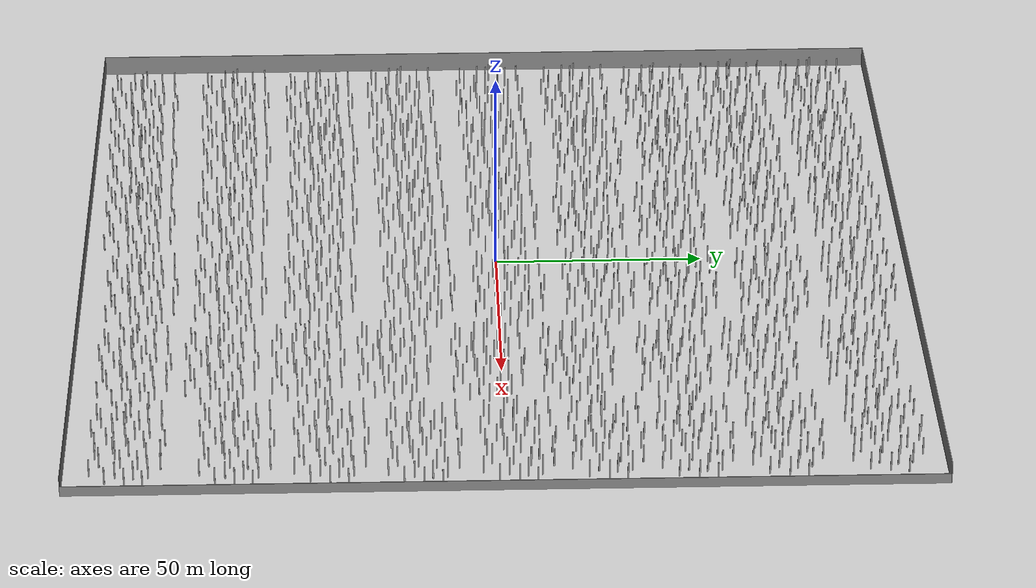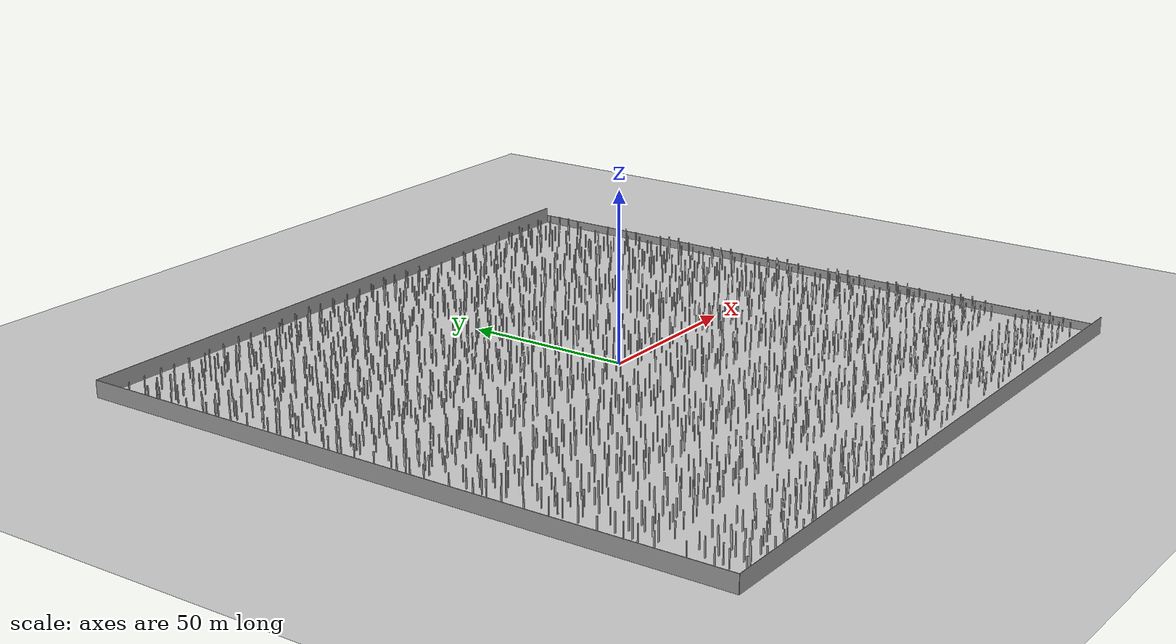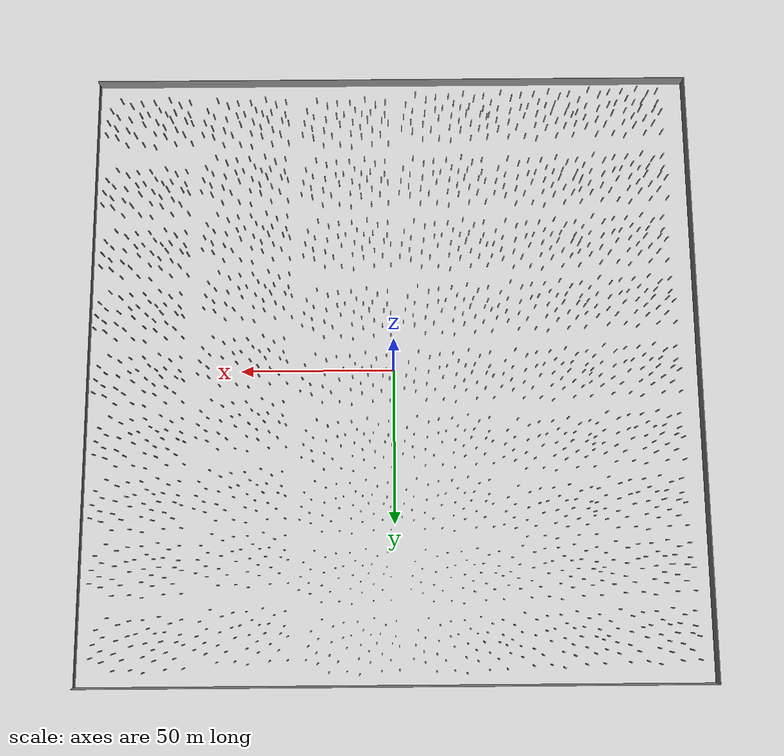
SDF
<sdf version="1.6">
 <world name="default">
  <light name="sun" type="directional">
   <pose>0 0 10 0 -0 0</pose>
   <diffuse>0.8 0.8 0.8 1</diffuse>
   <specular>0.2 0.2 0.2 1</specular>
   <attenuation>
    <range>1000</range>
    <constant>0.9</constant>
    <linear>0.01</linear>
    <quadratic>0.001</quadratic>
   </attenuation>
   <direction>-0.5 0.1 -0.9</direction>
  </light>
  <model name="ground_plane">
   <static>1</static>
   <link name="link">
    <collision name="collision">
     <geometry><plane><normal>0 0 1</normal><size>100 100</size></plane></geometry>
     <surface><friction><ode><mu>100</mu><mu2>50</mu2></ode></friction></surface>
    </collision>
    <visual name="visual">
     <cast_shadows>0</cast_shadows>
     <geometry><plane><normal>0 0 1</normal><size>100 100</size></plane></geometry>
     <material>
      <script><uri>file://media/materials/scripts/gazebo.material</uri><name>Gazebo/Grey</name></script>
     </material>
    </visual>
   </link>
  </model>
  <gravity>0 0 -9.8</gravity>
  <magnetic_field>6e-06 2.3e-05 -4.2e-05</magnetic_field>
  <atmosphere type="adiabatic"/>
  <physics name="default_physics" default="0" type="ode">
   <max_step_size>0.001</max_step_size>
   <real_time_factor>1</real_time_factor>
   <real_time_update_rate>1000</real_time_update_rate>
  </physics>
  <scene><ambient>0.4 0.4 0.4 1</ambient><background>0.7 0.7 0.7 1</background><shadows>1</shadows></scene>
  <audio><device>default</device></audio>
  <spherical_coordinates>
   <surface_model>EARTH_WGS84</surface_model>
   <latitude_deg>0</latitude_deg>
   <longitude_deg>0</longitude_deg>
   <elevation>0</elevation>
   <heading_deg>0</heading_deg>
  </spherical_coordinates>
  <model name="new_200">
   <link name="Wall_0">
    <pose>0 -100 0 0 -0 0</pose>
    <visual name="Wall_0_Visual">
     <pose>0 0 2.5 0 -0 0</pose>
     <geometry><box><size>200.15 0.15 5</size></box></geometry>
     <material>
      <script><uri>file://media/materials/scripts/gazebo.material</uri><name>Gazebo/Grey</name></script>
      <ambient>1 1 1 1</ambient>
     </material>
     <meta><layer>0</layer></meta>
    </visual>
    <collision name="Wall_0_Collision">
     <pose>0 0 2.5 0 -0 0</pose>
     <geometry><box><size>200.15 0.15 5</size></box></geometry>
     <surface>
      <friction>
       <ode><mu>1</mu><mu2>1</mu2><fdir1>0 0 0</fdir1><slip1>0</slip1><slip2>0</slip2></ode>
       <torsional>
        <coefficient>1</coefficient>
        <patch_radius>0</patch_radius>
        <surface_radius>0</surface_radius>
        <use_patch_radius>1</use_patch_radius>
        <ode><slip>0</slip></ode>
       </torsional>
      </friction>
      <bounce><restitution_coefficient>0</restitution_coefficient><threshold>1e+06</threshold></bounce>
      <contact>
       <collide_without_contact>0</collide_without_contact>
       <collide_without_contact_bitmask>1</collide_without_contact_bitmask>
       <collide_bitmask>1</collide_bitmask>
       <ode>
        <soft_cfm>0</soft_cfm>
        <soft_erp>0.2</soft_erp>
        <kp>1e+13</kp>
        <kd>1</kd>
        <max_vel>0.01</max_vel>
        <min_depth>0</min_depth>
       </ode>
       <bullet>
        <split_impulse>1</split_impulse>
        <split_impulse_penetration_threshold>-0.01</split_impulse_penetration_threshold>
        <soft_cfm>0</soft_cfm>
        <soft_erp>0.2</soft_erp>
        <kp>1e+13</kp>
        <kd>1</kd>
       </bullet>
      </contact>
     </surface>
    </collision>
   </link>
   <link name="Wall_2">
    <pose>-100 0 0 0 -0 1.5708</pose>
    <visual name="Wall_2_Visual">
     <pose>0 0 2.5 0 -0 0</pose>
     <geometry><box><size>200.15 0.15 5</size></box></geometry>
     <material>
      <script><uri>file://media/materials/scripts/gazebo.material</uri><name>Gazebo/Grey</name></script>
      <ambient>1 1 1 1</ambient>
     </material>
     <meta><layer>0</layer></meta>
    </visual>
    <collision name="Wall_2_Collision">
     <pose>0 0 2.5 0 -0 0</pose>
     <geometry><box><size>200.15 0.15 5</size></box></geometry>
     <surface>
      <friction>
       <ode><mu>1</mu><mu2>1</mu2><fdir1>0 0 0</fdir1><slip1>0</slip1><slip2>0</slip2></ode>
       <torsional>
        <coefficient>1</coefficient>
        <patch_radius>0</patch_radius>
        <surface_radius>0</surface_radius>
        <use_patch_radius>1</use_patch_radius>
        <ode><slip>0</slip></ode>
       </torsional>
      </friction>
      <bounce><restitution_coefficient>0</restitution_coefficient><threshold>1e+06</threshold></bounce>
      <contact>
       <collide_without_contact>0</collide_without_contact>
       <collide_without_contact_bitmask>1</collide_without_contact_bitmask>
       <collide_bitmask>1</collide_bitmask>
       <ode>
        <soft_cfm>0</soft_cfm>
        <soft_erp>0.2</soft_erp>
        <kp>1e+13</kp>
        <kd>1</kd>
        <max_vel>0.01</max_vel>
        <min_depth>0</min_depth>
       </ode>
       <bullet>
        <split_impulse>1</split_impulse>
        <split_impulse_penetration_threshold>-0.01</split_impulse_penetration_threshold>
        <soft_cfm>0</soft_cfm>
        <soft_erp>0.2</soft_erp>
        <kp>1e+13</kp>
        <kd>1</kd>
       </bullet>
      </contact>
     </surface>
    </collision>
   </link>
   <link name="Wall_4">
    <pose>0 100 0 0 -0 0</pose>
    <visual name="Wall_4_Visual">
     <pose>0 0 2.5 0 -0 0</pose>
     <geometry><box><size>200.15 0.15 5</size></box></geometry>
     <material>
      <script><uri>file://media/materials/scripts/gazebo.material</uri><name>Gazebo/Grey</name></script>
      <ambient>1 1 1 1</ambient>
     </material>
     <meta><layer>0</layer></meta>
    </visual>
    <collision name="Wall_4_Collision">
     <pose>0 0 2.5 0 -0 0</pose>
     <geometry><box><size>200.15 0.15 5</size></box></geometry>
     <surface>
      <friction>
       <ode><mu>1</mu><mu2>1</mu2><fdir1>0 0 0</fdir1><slip1>0</slip1><slip2>0</slip2></ode>
       <torsional>
        <coefficient>1</coefficient>
        <patch_radius>0</patch_radius>
        <surface_radius>0</surface_radius>
        <use_patch_radius>1</use_patch_radius>
        <ode><slip>0</slip></ode>
       </torsional>
      </friction>
      <bounce><restitution_coefficient>0</restitution_coefficient><threshold>1e+06</threshold></bounce>
      <contact>
       <collide_without_contact>0</collide_without_contact>
       <collide_without_contact_bitmask>1</collide_without_contact_bitmask>
       <collide_bitmask>1</collide_bitmask>
       <ode>
        <soft_cfm>0</soft_cfm>
        <soft_erp>0.2</soft_erp>
        <kp>1e+13</kp>
        <kd>1</kd>
        <max_vel>0.01</max_vel>
        <min_depth>0</min_depth>
       </ode>
       <bullet>
        <split_impulse>1</split_impulse>
        <split_impulse_penetration_threshold>-0.01</split_impulse_penetration_threshold>
        <soft_cfm>0</soft_cfm>
        <soft_erp>0.2</soft_erp>
        <kp>1e+13</kp>
        <kd>1</kd>
       </bullet>
      </contact>
     </surface>
    </collision>
   </link>
   <link name="Wall_6">
    <pose>100 0 0 0 -0 1.5708</pose>
    <visual name="Wall_6_Visual">
     <pose>0 0 1.25 0 -0 0</pose>
     <geometry><box><size>200.15 0.15 2.5</size></box></geometry>
     <material>
      <script><uri>file://media/materials/scripts/gazebo.material</uri><name>Gazebo/Grey</name></script>
      <ambient>1 1 1 1</ambient>
     </material>
     <meta><layer>0</layer></meta>
    </visual>
    <collision name="Wall_6_Collision">
     <pose>0 0 1.25 0 -0 0</pose>
     <geometry><box><size>200.15 0.15 2.5</size></box></geometry>
     <surface>
      <friction>
       <ode><mu>1</mu><mu2>1</mu2><fdir1>0 0 0</fdir1><slip1>0</slip1><slip2>0</slip2></ode>
       <torsional>
        <coefficient>1</coefficient>
        <patch_radius>0</patch_radius>
        <surface_radius>0</surface_radius>
        <use_patch_radius>1</use_patch_radius>
        <ode><slip>0</slip></ode>
       </torsional>
      </friction>
      <bounce><restitution_coefficient>0</restitution_coefficient><threshold>1e+06</threshold></bounce>
      <contact>
       <collide_without_contact>0</collide_without_contact>
       <collide_without_contact_bitmask>1</collide_without_contact_bitmask>
       <collide_bitmask>1</collide_bitmask>
       <ode>
        <soft_cfm>0</soft_cfm>
        <soft_erp>0.2</soft_erp>
        <kp>1e+13</kp>
        <kd>1</kd>
        <max_vel>0.01</max_vel>
        <min_depth>0</min_depth>
       </ode>
       <bullet>
        <split_impulse>1</split_impulse>
        <split_impulse_penetration_threshold>-0.01</split_impulse_penetration_threshold>
        <soft_cfm>0</soft_cfm>
        <soft_erp>0.2</soft_erp>
        <kp>1e+13</kp>
        <kd>1</kd>
       </bullet>
      </contact>
     </surface>
    </collision>
   </link>
   <static>1</static>
   <pose>0.131028 -0.240999 0 0 -0 0</pose>
  </model>
  <model name="pillars">
   <link name="body">
    <velocity_decay><linear>0</linear><angular>0</angular></velocity_decay>
    <visual name="visual">
     <pose>0 0 -0.001 0 -0 0</pose>
     <geometry><mesh><uri>model://pillars/pillars4.dae</uri><scale>1 1 1</scale></mesh></geometry>
    </visual>
    <collision name="pillars">
     <pose>0 0 -0.001 0 -0 0</pose>
     <geometry>
      <mesh>
       <uri>/home/huiyulin/Coding/TARE/multi_planning/Simulator/mrsl2_ws/src/mrsl_quadrotor/mrsl_models/models/pillars/pillars4.dae</uri>
       <scale>1 1 1</scale>
      </mesh>
     </geometry>
     <surface>
      <friction>
       <ode><mu>1</mu><mu2>1</mu2><fdir1>0 0 0</fdir1><slip1>0</slip1><slip2>0</slip2></ode>
       <torsional>
        <coefficient>1</coefficient>
        <patch_radius>0</patch_radius>
        <surface_radius>0</surface_radius>
        <use_patch_radius>1</use_patch_radius>
        <ode><slip>0</slip></ode>
       </torsional>
      </friction>
      <bounce><restitution_coefficient>0</restitution_coefficient><threshold>1e+06</threshold></bounce>
      <contact>
       <collide_without_contact>0</collide_without_contact>
       <collide_without_contact_bitmask>1</collide_without_contact_bitmask>
       <collide_bitmask>1</collide_bitmask>
       <ode>
        <soft_cfm>0</soft_cfm>
        <soft_erp>0.2</soft_erp>
        <kp>1e+13</kp>
        <kd>1</kd>
        <max_vel>0.01</max_vel>
        <min_depth>0</min_depth>
       </ode>
       <bullet>
        <split_impulse>1</split_impulse>
        <split_impulse_penetration_threshold>-0.01</split_impulse_penetration_threshold>
        <soft_cfm>0</soft_cfm>
        <soft_erp>0.2</soft_erp>
        <kp>1e+13</kp>
        <kd>1</kd>
       </bullet>
      </contact>
     </surface>
    </collision>
   </link>
   <static>1</static>
   <pose>63.8836 85.888 0 0 -0 0</pose>
  </model>
  <model name="pillars_clone">
   <link name="body">
    <velocity_decay><linear>0</linear><angular>0</angular></velocity_decay>
    <visual name="visual">
     <pose>0 0 -0.001 0 -0 0</pose>
     <geometry><mesh><uri>model://pillars/pillars4.dae</uri><scale>1 1 1</scale></mesh></geometry>
    </visual>
    <collision name="pillars">
     <pose>0 0 -0.001 0 -0 0</pose>
     <geometry>
      <mesh>
       <uri>/home/huiyulin/Coding/TARE/multi_planning/Simulator/mrsl2_ws/src/mrsl_quadrotor/mrsl_models/models/pillars/pillars4.dae</uri>
       <scale>1 1 1</scale>
      </mesh>
     </geometry>
     <surface>
      <friction>
       <ode><mu>1</mu><mu2>1</mu2><fdir1>0 0 0</fdir1><slip1>0</slip1><slip2>0</slip2></ode>
       <torsional>
        <coefficient>1</coefficient>
        <patch_radius>0</patch_radius>
        <surface_radius>0</surface_radius>
        <use_patch_radius>1</use_patch_radius>
        <ode><slip>0</slip></ode>
       </torsional>
      </friction>
      <bounce><restitution_coefficient>0</restitution_coefficient><threshold>1e+06</threshold></bounce>
      <contact>
       <collide_without_contact>0</collide_without_contact>
       <collide_without_contact_bitmask>1</collide_without_contact_bitmask>
       <collide_bitmask>1</collide_bitmask>
       <ode>
        <soft_cfm>0</soft_cfm>
        <soft_erp>0.2</soft_erp>
        <kp>1e+13</kp>
        <kd>1</kd>
        <max_vel>0.01</max_vel>
        <min_depth>0</min_depth>
       </ode>
       <bullet>
        <split_impulse>1</split_impulse>
        <split_impulse_penetration_threshold>-0.01</split_impulse_penetration_threshold>
        <soft_cfm>0</soft_cfm>
        <soft_erp>0.2</soft_erp>
        <kp>1e+13</kp>
        <kd>1</kd>
       </bullet>
      </contact>
     </surface>
    </collision>
   </link>
   <static>1</static>
   <pose>65.0825 63.0175 0 0 -0 0</pose>
  </model>
  <model name="pillars_clone_0">
   <link name="body">
    <velocity_decay><linear>0</linear><angular>0</angular></velocity_decay>
    <visual name="visual">
     <pose>0 0 -0.001 0 -0 0</pose>
     <geometry><mesh><uri>model://pillars/pillars4.dae</uri><scale>1 1 1</scale></mesh></geometry>
    </visual>
    <collision name="pillars">
     <pose>0 0 -0.001 0 -0 0</pose>
     <geometry>
      <mesh>
       <uri>/home/huiyulin/Coding/TARE/multi_planning/Simulator/mrsl2_ws/src/mrsl_quadrotor/mrsl_models/models/pillars/pillars4.dae</uri>
       <scale>1 1 1</scale>
      </mesh>
     </geometry>
     <surface>
      <friction>
       <ode><mu>1</mu><mu2>1</mu2><fdir1>0 0 0</fdir1><slip1>0</slip1><slip2>0</slip2></ode>
       <torsional>
        <coefficient>1</coefficient>
        <patch_radius>0</patch_radius>
        <surface_radius>0</surface_radius>
        <use_patch_radius>1</use_patch_radius>
        <ode><slip>0</slip></ode>
       </torsional>
      </friction>
      <bounce><restitution_coefficient>0</restitution_coefficient><threshold>1e+06</threshold></bounce>
      <contact>
       <collide_without_contact>0</collide_without_contact>
       <collide_without_contact_bitmask>1</collide_without_contact_bitmask>
       <collide_bitmask>1</collide_bitmask>
       <ode>
        <soft_cfm>0</soft_cfm>
        <soft_erp>0.2</soft_erp>
        <kp>1e+13</kp>
        <kd>1</kd>
        <max_vel>0.01</max_vel>
        <min_depth>0</min_depth>
       </ode>
       <bullet>
        <split_impulse>1</split_impulse>
        <split_impulse_penetration_threshold>-0.01</split_impulse_penetration_threshold>
        <soft_cfm>0</soft_cfm>
        <soft_erp>0.2</soft_erp>
        <kp>1e+13</kp>
        <kd>1</kd>
       </bullet>
      </contact>
     </surface>
    </collision>
   </link>
   <static>1</static>
   <pose>65.7574 42.5502 0 0 -0 0</pose>
  </model>
  <model name="pillars_clone_1">
   <link name="body">
    <velocity_decay><linear>0</linear><angular>0</angular></velocity_decay>
    <visual name="visual">
     <pose>0 0 -0.001 0 -0 0</pose>
     <geometry><mesh><uri>model://pillars/pillars4.dae</uri><scale>1 1 1</scale></mesh></geometry>
    </visual>
    <collision name="pillars">
     <pose>0 0 -0.001 0 -0 0</pose>
     <geometry>
      <mesh>
       <uri>/home/huiyulin/Coding/TARE/multi_planning/Simulator/mrsl2_ws/src/mrsl_quadrotor/mrsl_models/models/pillars/pillars4.dae</uri>
       <scale>1 1 1</scale>
      </mesh>
     </geometry>
     <surface>
      <friction>
       <ode><mu>1</mu><mu2>1</mu2><fdir1>0 0 0</fdir1><slip1>0</slip1><slip2>0</slip2></ode>
       <torsional>
        <coefficient>1</coefficient>
        <patch_radius>0</patch_radius>
        <surface_radius>0</surface_radius>
        <use_patch_radius>1</use_patch_radius>
        <ode><slip>0</slip></ode>
       </torsional>
      </friction>
      <bounce><restitution_coefficient>0</restitution_coefficient><threshold>1e+06</threshold></bounce>
      <contact>
       <collide_without_contact>0</collide_without_contact>
       <collide_without_contact_bitmask>1</collide_without_contact_bitmask>
       <collide_bitmask>1</collide_bitmask>
       <ode>
        <soft_cfm>0</soft_cfm>
        <soft_erp>0.2</soft_erp>
        <kp>1e+13</kp>
        <kd>1</kd>
        <max_vel>0.01</max_vel>
        <min_depth>0</min_depth>
       </ode>
       <bullet>
        <split_impulse>1</split_impulse>
        <split_impulse_penetration_threshold>-0.01</split_impulse_penetration_threshold>
        <soft_cfm>0</soft_cfm>
        <soft_erp>0.2</soft_erp>
        <kp>1e+13</kp>
        <kd>1</kd>
       </bullet>
      </contact>
     </surface>
    </collision>
   </link>
   <static>1</static>
   <pose>65.3502 22.278 0 0 -0 0</pose>
  </model>
  <model name="pillars_clone_2">
   <link name="body">
    <velocity_decay><linear>0</linear><angular>0</angular></velocity_decay>
    <visual name="visual">
     <pose>0 0 -0.001 0 -0 0</pose>
     <geometry><mesh><uri>model://pillars/pillars4.dae</uri><scale>1 1 1</scale></mesh></geometry>
    </visual>
    <collision name="pillars">
     <pose>0 0 -0.001 0 -0 0</pose>
     <geometry>
      <mesh>
       <uri>/home/huiyulin/Coding/TARE/multi_planning/Simulator/mrsl2_ws/src/mrsl_quadrotor/mrsl_models/models/pillars/pillars4.dae</uri>
       <scale>1 1 1</scale>
      </mesh>
     </geometry>
     <surface>
      <friction>
       <ode><mu>1</mu><mu2>1</mu2><fdir1>0 0 0</fdir1><slip1>0</slip1><slip2>0</slip2></ode>
       <torsional>
        <coefficient>1</coefficient>
        <patch_radius>0</patch_radius>
        <surface_radius>0</surface_radius>
        <use_patch_radius>1</use_patch_radius>
        <ode><slip>0</slip></ode>
       </torsional>
      </friction>
      <bounce><restitution_coefficient>0</restitution_coefficient><threshold>1e+06</threshold></bounce>
      <contact>
       <collide_without_contact>0</collide_without_contact>
       <collide_without_contact_bitmask>1</collide_without_contact_bitmask>
       <collide_bitmask>1</collide_bitmask>
       <ode>
        <soft_cfm>0</soft_cfm>
        <soft_erp>0.2</soft_erp>
        <kp>1e+13</kp>
        <kd>1</kd>
        <max_vel>0.01</max_vel>
        <min_depth>0</min_depth>
       </ode>
       <bullet>
        <split_impulse>1</split_impulse>
        <split_impulse_penetration_threshold>-0.01</split_impulse_penetration_threshold>
        <soft_cfm>0</soft_cfm>
        <soft_erp>0.2</soft_erp>
        <kp>1e+13</kp>
        <kd>1</kd>
       </bullet>
      </contact>
     </surface>
    </collision>
   </link>
   <static>1</static>
   <pose>66.4072 2.03271 0 0 -0 0</pose>
  </model>
  <model name="pillars_clone_3">
   <link name="body">
    <velocity_decay><linear>0</linear><angular>0</angular></velocity_decay>
    <visual name="visual">
     <pose>0 0 -0.001 0 -0 0</pose>
     <geometry><mesh><uri>model://pillars/pillars4.dae</uri><scale>1 1 1</scale></mesh></geometry>
    </visual>
    <collision name="pillars">
     <pose>0 0 -0.001 0 -0 0</pose>
     <geometry>
      <mesh>
       <uri>/home/huiyulin/Coding/TARE/multi_planning/Simulator/mrsl2_ws/src/mrsl_quadrotor/mrsl_models/models/pillars/pillars4.dae</uri>
       <scale>1 1 1</scale>
      </mesh>
     </geometry>
     <surface>
      <friction>
       <ode><mu>1</mu><mu2>1</mu2><fdir1>0 0 0</fdir1><slip1>0</slip1><slip2>0</slip2></ode>
       <torsional>
        <coefficient>1</coefficient>
        <patch_radius>0</patch_radius>
        <surface_radius>0</surface_radius>
        <use_patch_radius>1</use_patch_radius>
        <ode><slip>0</slip></ode>
       </torsional>
      </friction>
      <bounce><restitution_coefficient>0</restitution_coefficient><threshold>1e+06</threshold></bounce>
      <contact>
       <collide_without_contact>0</collide_without_contact>
       <collide_without_contact_bitmask>1</collide_without_contact_bitmask>
       <collide_bitmask>1</collide_bitmask>
       <ode>
        <soft_cfm>0</soft_cfm>
        <soft_erp>0.2</soft_erp>
        <kp>1e+13</kp>
        <kd>1</kd>
        <max_vel>0.01</max_vel>
        <min_depth>0</min_depth>
       </ode>
       <bullet>
        <split_impulse>1</split_impulse>
        <split_impulse_penetration_threshold>-0.01</split_impulse_penetration_threshold>
        <soft_cfm>0</soft_cfm>
        <soft_erp>0.2</soft_erp>
        <kp>1e+13</kp>
        <kd>1</kd>
       </bullet>
      </contact>
     </surface>
    </collision>
   </link>
   <static>1</static>
   <pose>66.9687 -19.4024 0 0 -0 0</pose>
  </model>
  <model name="pillars_clone_4">
   <link name="body">
    <velocity_decay><linear>0</linear><angular>0</angular></velocity_decay>
    <visual name="visual">
     <pose>0 0 -0.001 0 -0 0</pose>
     <geometry><mesh><uri>model://pillars/pillars4.dae</uri><scale>1 1 1</scale></mesh></geometry>
    </visual>
    <collision name="pillars">
     <pose>0 0 -0.001 0 -0 0</pose>
     <geometry>
      <mesh>
       <uri>/home/huiyulin/Coding/TARE/multi_planning/Simulator/mrsl2_ws/src/mrsl_quadrotor/mrsl_models/models/pillars/pillars4.dae</uri>
       <scale>1 1 1</scale>
      </mesh>
     </geometry>
     <surface>
      <friction>
       <ode><mu>1</mu><mu2>1</mu2><fdir1>0 0 0</fdir1><slip1>0</slip1><slip2>0</slip2></ode>
       <torsional>
        <coefficient>1</coefficient>
        <patch_radius>0</patch_radius>
        <surface_radius>0</surface_radius>
        <use_patch_radius>1</use_patch_radius>
        <ode><slip>0</slip></ode>
       </torsional>
      </friction>
      <bounce><restitution_coefficient>0</restitution_coefficient><threshold>1e+06</threshold></bounce>
      <contact>
       <collide_without_contact>0</collide_without_contact>
       <collide_without_contact_bitmask>1</collide_without_contact_bitmask>
       <collide_bitmask>1</collide_bitmask>
       <ode>
        <soft_cfm>0</soft_cfm>
        <soft_erp>0.2</soft_erp>
        <kp>1e+13</kp>
        <kd>1</kd>
        <max_vel>0.01</max_vel>
        <min_depth>0</min_depth>
       </ode>
       <bullet>
        <split_impulse>1</split_impulse>
        <split_impulse_penetration_threshold>-0.01</split_impulse_penetration_threshold>
        <soft_cfm>0</soft_cfm>
        <soft_erp>0.2</soft_erp>
        <kp>1e+13</kp>
        <kd>1</kd>
       </bullet>
      </contact>
     </surface>
    </collision>
   </link>
   <static>1</static>
   <pose>65.8561 -40.5548 0 0 -0 0</pose>
  </model>
  <model name="pillars_clone_5">
   <link name="body">
    <velocity_decay><linear>0</linear><angular>0</angular></velocity_decay>
    <visual name="visual">
     <pose>0 0 -0.001 0 -0 0</pose>
     <geometry><mesh><uri>model://pillars/pillars4.dae</uri><scale>1 1 1</scale></mesh></geometry>
    </visual>
    <collision name="pillars">
     <pose>0 0 -0.001 0 -0 0</pose>
     <geometry>
      <mesh>
       <uri>/home/huiyulin/Coding/TARE/multi_planning/Simulator/mrsl2_ws/src/mrsl_quadrotor/mrsl_models/models/pillars/pillars4.dae</uri>
       <scale>1 1 1</scale>
      </mesh>
     </geometry>
     <surface>
      <friction>
       <ode><mu>1</mu><mu2>1</mu2><fdir1>0 0 0</fdir1><slip1>0</slip1><slip2>0</slip2></ode>
       <torsional>
        <coefficient>1</coefficient>
        <patch_radius>0</patch_radius>
        <surface_radius>0</surface_radius>
        <use_patch_radius>1</use_patch_radius>
        <ode><slip>0</slip></ode>
       </torsional>
      </friction>
      <bounce><restitution_coefficient>0</restitution_coefficient><threshold>1e+06</threshold></bounce>
      <contact>
       <collide_without_contact>0</collide_without_contact>
       <collide_without_contact_bitmask>1</collide_without_contact_bitmask>
       <collide_bitmask>1</collide_bitmask>
       <ode>
        <soft_cfm>0</soft_cfm>
        <soft_erp>0.2</soft_erp>
        <kp>1e+13</kp>
        <kd>1</kd>
        <max_vel>0.01</max_vel>
        <min_depth>0</min_depth>
       </ode>
       <bullet>
        <split_impulse>1</split_impulse>
        <split_impulse_penetration_threshold>-0.01</split_impulse_penetration_threshold>
        <soft_cfm>0</soft_cfm>
        <soft_erp>0.2</soft_erp>
        <kp>1e+13</kp>
        <kd>1</kd>
       </bullet>
      </contact>
     </surface>
    </collision>
   </link>
   <static>1</static>
   <pose>66.1522 -62.0358 0 0 -0 0</pose>
  </model>
  <model name="pillars_clone_6">
   <link name="body">
    <velocity_decay><linear>0</linear><angular>0</angular></velocity_decay>
    <visual name="visual">
     <pose>0 0 -0.001 0 -0 0</pose>
     <geometry><mesh><uri>model://pillars/pillars4.dae</uri><scale>1 1 1</scale></mesh></geometry>
    </visual>
    <collision name="pillars">
     <pose>0 0 -0.001 0 -0 0</pose>
     <geometry>
      <mesh>
       <uri>/home/huiyulin/Coding/TARE/multi_planning/Simulator/mrsl2_ws/src/mrsl_quadrotor/mrsl_models/models/pillars/pillars4.dae</uri>
       <scale>1 1 1</scale>
      </mesh>
     </geometry>
     <surface>
      <friction>
       <ode><mu>1</mu><mu2>1</mu2><fdir1>0 0 0</fdir1><slip1>0</slip1><slip2>0</slip2></ode>
       <torsional>
        <coefficient>1</coefficient>
        <patch_radius>0</patch_radius>
        <surface_radius>0</surface_radius>
        <use_patch_radius>1</use_patch_radius>
        <ode><slip>0</slip></ode>
       </torsional>
      </friction>
      <bounce><restitution_coefficient>0</restitution_coefficient><threshold>1e+06</threshold></bounce>
      <contact>
       <collide_without_contact>0</collide_without_contact>
       <collide_without_contact_bitmask>1</collide_without_contact_bitmask>
       <collide_bitmask>1</collide_bitmask>
       <ode>
        <soft_cfm>0</soft_cfm>
        <soft_erp>0.2</soft_erp>
        <kp>1e+13</kp>
        <kd>1</kd>
        <max_vel>0.01</max_vel>
        <min_depth>0</min_depth>
       </ode>
       <bullet>
        <split_impulse>1</split_impulse>
        <split_impulse_penetration_threshold>-0.01</split_impulse_penetration_threshold>
        <soft_cfm>0</soft_cfm>
        <soft_erp>0.2</soft_erp>
        <kp>1e+13</kp>
        <kd>1</kd>
       </bullet>
      </contact>
     </surface>
    </collision>
   </link>
   <static>1</static>
   <pose>65.6273 -86.881 0 0 -0 0</pose>
  </model>
  <model name="pillars_clone_7">
   <link name="body">
    <velocity_decay><linear>0</linear><angular>0</angular></velocity_decay>
    <visual name="visual">
     <pose>0 0 -0.001 0 -0 0</pose>
     <geometry><mesh><uri>model://pillars/pillars4.dae</uri><scale>1 1 1</scale></mesh></geometry>
    </visual>
    <collision name="pillars">
     <pose>0 0 -0.001 0 -0 0</pose>
     <geometry>
      <mesh>
       <uri>/home/huiyulin/Coding/TARE/multi_planning/Simulator/mrsl2_ws/src/mrsl_quadrotor/mrsl_models/models/pillars/pillars4.dae</uri>
       <scale>1 1 1</scale>
      </mesh>
     </geometry>
     <surface>
      <friction>
       <ode><mu>1</mu><mu2>1</mu2><fdir1>0 0 0</fdir1><slip1>0</slip1><slip2>0</slip2></ode>
       <torsional>
        <coefficient>1</coefficient>
        <patch_radius>0</patch_radius>
        <surface_radius>0</surface_radius>
        <use_patch_radius>1</use_patch_radius>
        <ode><slip>0</slip></ode>
       </torsional>
      </friction>
      <bounce><restitution_coefficient>0</restitution_coefficient><threshold>1e+06</threshold></bounce>
      <contact>
       <collide_without_contact>0</collide_without_contact>
       <collide_without_contact_bitmask>1</collide_without_contact_bitmask>
       <collide_bitmask>1</collide_bitmask>
       <ode>
        <soft_cfm>0</soft_cfm>
        <soft_erp>0.2</soft_erp>
        <kp>1e+13</kp>
        <kd>1</kd>
        <max_vel>0.01</max_vel>
        <min_depth>0</min_depth>
       </ode>
       <bullet>
        <split_impulse>1</split_impulse>
        <split_impulse_penetration_threshold>-0.01</split_impulse_penetration_threshold>
        <soft_cfm>0</soft_cfm>
        <soft_erp>0.2</soft_erp>
        <kp>1e+13</kp>
        <kd>1</kd>
       </bullet>
      </contact>
     </surface>
    </collision>
   </link>
   <static>1</static>
   <pose>32.8257 -86.7839 0 0 -0 0</pose>
  </model>
  <model name="pillars_clone_8">
   <link name="body">
    <velocity_decay><linear>0</linear><angular>0</angular></velocity_decay>
    <visual name="visual">
     <pose>0 0 -0.001 0 -0 0</pose>
     <geometry><mesh><uri>model://pillars/pillars4.dae</uri><scale>1 1 1</scale></mesh></geometry>
    </visual>
    <collision name="pillars">
     <pose>0 0 -0.001 0 -0 0</pose>
     <geometry>
      <mesh>
       <uri>/home/huiyulin/Coding/TARE/multi_planning/Simulator/mrsl2_ws/src/mrsl_quadrotor/mrsl_models/models/pillars/pillars4.dae</uri>
       <scale>1 1 1</scale>
      </mesh>
     </geometry>
     <surface>
      <friction>
       <ode><mu>1</mu><mu2>1</mu2><fdir1>0 0 0</fdir1><slip1>0</slip1><slip2>0</slip2></ode>
       <torsional>
        <coefficient>1</coefficient>
        <patch_radius>0</patch_radius>
        <surface_radius>0</surface_radius>
        <use_patch_radius>1</use_patch_radius>
        <ode><slip>0</slip></ode>
       </torsional>
      </friction>
      <bounce><restitution_coefficient>0</restitution_coefficient><threshold>1e+06</threshold></bounce>
      <contact>
       <collide_without_contact>0</collide_without_contact>
       <collide_without_contact_bitmask>1</collide_without_contact_bitmask>
       <collide_bitmask>1</collide_bitmask>
       <ode>
        <soft_cfm>0</soft_cfm>
        <soft_erp>0.2</soft_erp>
        <kp>1e+13</kp>
        <kd>1</kd>
        <max_vel>0.01</max_vel>
        <min_depth>0</min_depth>
       </ode>
       <bullet>
        <split_impulse>1</split_impulse>
        <split_impulse_penetration_threshold>-0.01</split_impulse_penetration_threshold>
        <soft_cfm>0</soft_cfm>
        <soft_erp>0.2</soft_erp>
        <kp>1e+13</kp>
        <kd>1</kd>
       </bullet>
      </contact>
     </surface>
    </collision>
   </link>
   <static>1</static>
   <pose>32.8636 -66.322 0 0 -0 0</pose>
  </model>
  <model name="pillars_clone_9">
   <link name="body">
    <velocity_decay><linear>0</linear><angular>0</angular></velocity_decay>
    <visual name="visual">
     <pose>0 0 -0.001 0 -0 0</pose>
     <geometry><mesh><uri>model://pillars/pillars4.dae</uri><scale>1 1 1</scale></mesh></geometry>
    </visual>
    <collision name="pillars">
     <pose>0 0 -0.001 0 -0 0</pose>
     <geometry>
      <mesh>
       <uri>/home/huiyulin/Coding/TARE/multi_planning/Simulator/mrsl2_ws/src/mrsl_quadrotor/mrsl_models/models/pillars/pillars4.dae</uri>
       <scale>1 1 1</scale>
      </mesh>
     </geometry>
     <surface>
      <friction>
       <ode><mu>1</mu><mu2>1</mu2><fdir1>0 0 0</fdir1><slip1>0</slip1><slip2>0</slip2></ode>
       <torsional>
        <coefficient>1</coefficient>
        <patch_radius>0</patch_radius>
        <surface_radius>0</surface_radius>
        <use_patch_radius>1</use_patch_radius>
        <ode><slip>0</slip></ode>
       </torsional>
      </friction>
      <bounce><restitution_coefficient>0</restitution_coefficient><threshold>1e+06</threshold></bounce>
      <contact>
       <collide_without_contact>0</collide_without_contact>
       <collide_without_contact_bitmask>1</collide_without_contact_bitmask>
       <collide_bitmask>1</collide_bitmask>
       <ode>
        <soft_cfm>0</soft_cfm>
        <soft_erp>0.2</soft_erp>
        <kp>1e+13</kp>
        <kd>1</kd>
        <max_vel>0.01</max_vel>
        <min_depth>0</min_depth>
       </ode>
       <bullet>
        <split_impulse>1</split_impulse>
        <split_impulse_penetration_threshold>-0.01</split_impulse_penetration_threshold>
        <soft_cfm>0</soft_cfm>
        <soft_erp>0.2</soft_erp>
        <kp>1e+13</kp>
        <kd>1</kd>
       </bullet>
      </contact>
     </surface>
    </collision>
   </link>
   <static>1</static>
   <pose>32.0594 -46.1445 0 0 -0 0</pose>
  </model>
  <model name="pillars_clone_10">
   <link name="body">
    <velocity_decay><linear>0</linear><angular>0</angular></velocity_decay>
    <visual name="visual">
     <pose>0 0 -0.001 0 -0 0</pose>
     <geometry><mesh><uri>model://pillars/pillars4.dae</uri><scale>1 1 1</scale></mesh></geometry>
    </visual>
    <collision name="pillars">
     <pose>0 0 -0.001 0 -0 0</pose>
     <geometry>
      <mesh>
       <uri>/home/huiyulin/Coding/TARE/multi_planning/Simulator/mrsl2_ws/src/mrsl_quadrotor/mrsl_models/models/pillars/pillars4.dae</uri>
       <scale>1 1 1</scale>
      </mesh>
     </geometry>
     <surface>
      <friction>
       <ode><mu>1</mu><mu2>1</mu2><fdir1>0 0 0</fdir1><slip1>0</slip1><slip2>0</slip2></ode>
       <torsional>
        <coefficient>1</coefficient>
        <patch_radius>0</patch_radius>
        <surface_radius>0</surface_radius>
        <use_patch_radius>1</use_patch_radius>
        <ode><slip>0</slip></ode>
       </torsional>
      </friction>
      <bounce><restitution_coefficient>0</restitution_coefficient><threshold>1e+06</threshold></bounce>
      <contact>
       <collide_without_contact>0</collide_without_contact>
       <collide_without_contact_bitmask>1</collide_without_contact_bitmask>
       <collide_bitmask>1</collide_bitmask>
       <ode>
        <soft_cfm>0</soft_cfm>
        <soft_erp>0.2</soft_erp>
        <kp>1e+13</kp>
        <kd>1</kd>
        <max_vel>0.01</max_vel>
        <min_depth>0</min_depth>
       </ode>
       <bullet>
        <split_impulse>1</split_impulse>
        <split_impulse_penetration_threshold>-0.01</split_impulse_penetration_threshold>
        <soft_cfm>0</soft_cfm>
        <soft_erp>0.2</soft_erp>
        <kp>1e+13</kp>
        <kd>1</kd>
       </bullet>
      </contact>
     </surface>
    </collision>
   </link>
   <static>1</static>
   <pose>31.1453 -25.9971 0 0 -0 0</pose>
  </model>
  <model name="pillars_clone_11">
   <link name="body">
    <velocity_decay><linear>0</linear><angular>0</angular></velocity_decay>
    <visual name="visual">
     <pose>0 0 -0.001 0 -0 0</pose>
     <geometry><mesh><uri>model://pillars/pillars4.dae</uri><scale>1 1 1</scale></mesh></geometry>
    </visual>
    <collision name="pillars">
     <pose>0 0 -0.001 0 -0 0</pose>
     <geometry>
      <mesh>
       <uri>/home/huiyulin/Coding/TARE/multi_planning/Simulator/mrsl2_ws/src/mrsl_quadrotor/mrsl_models/models/pillars/pillars4.dae</uri>
       <scale>1 1 1</scale>
      </mesh>
     </geometry>
     <surface>
      <friction>
       <ode><mu>1</mu><mu2>1</mu2><fdir1>0 0 0</fdir1><slip1>0</slip1><slip2>0</slip2></ode>
       <torsional>
        <coefficient>1</coefficient>
        <patch_radius>0</patch_radius>
        <surface_radius>0</surface_radius>
        <use_patch_radius>1</use_patch_radius>
        <ode><slip>0</slip></ode>
       </torsional>
      </friction>
      <bounce><restitution_coefficient>0</restitution_coefficient><threshold>1e+06</threshold></bounce>
      <contact>
       <collide_without_contact>0</collide_without_contact>
       <collide_without_contact_bitmask>1</collide_without_contact_bitmask>
       <collide_bitmask>1</collide_bitmask>
       <ode>
        <soft_cfm>0</soft_cfm>
        <soft_erp>0.2</soft_erp>
        <kp>1e+13</kp>
        <kd>1</kd>
        <max_vel>0.01</max_vel>
        <min_depth>0</min_depth>
       </ode>
       <bullet>
        <split_impulse>1</split_impulse>
        <split_impulse_penetration_threshold>-0.01</split_impulse_penetration_threshold>
        <soft_cfm>0</soft_cfm>
        <soft_erp>0.2</soft_erp>
        <kp>1e+13</kp>
        <kd>1</kd>
       </bullet>
      </contact>
     </surface>
    </collision>
   </link>
   <static>1</static>
   <pose>32.5652 -3.96804 0 0 -0 0</pose>
  </model>
  <model name="pillars_clone_12">
   <link name="body">
    <velocity_decay><linear>0</linear><angular>0</angular></velocity_decay>
    <visual name="visual">
     <pose>0 0 -0.001 0 -0 0</pose>
     <geometry><mesh><uri>model://pillars/pillars4.dae</uri><scale>1 1 1</scale></mesh></geometry>
    </visual>
    <collision name="pillars">
     <pose>0 0 -0.001 0 -0 0</pose>
     <geometry>
      <mesh>
       <uri>/home/huiyulin/Coding/TARE/multi_planning/Simulator/mrsl2_ws/src/mrsl_quadrotor/mrsl_models/models/pillars/pillars4.dae</uri>
       <scale>1 1 1</scale>
      </mesh>
     </geometry>
     <surface>
      <friction>
       <ode><mu>1</mu><mu2>1</mu2><fdir1>0 0 0</fdir1><slip1>0</slip1><slip2>0</slip2></ode>
       <torsional>
        <coefficient>1</coefficient>
        <patch_radius>0</patch_radius>
        <surface_radius>0</surface_radius>
        <use_patch_radius>1</use_patch_radius>
        <ode><slip>0</slip></ode>
       </torsional>
      </friction>
      <bounce><restitution_coefficient>0</restitution_coefficient><threshold>1e+06</threshold></bounce>
      <contact>
       <collide_without_contact>0</collide_without_contact>
       <collide_without_contact_bitmask>1</collide_without_contact_bitmask>
       <collide_bitmask>1</collide_bitmask>
       <ode>
        <soft_cfm>0</soft_cfm>
        <soft_erp>0.2</soft_erp>
        <kp>1e+13</kp>
        <kd>1</kd>
        <max_vel>0.01</max_vel>
        <min_depth>0</min_depth>
       </ode>
       <bullet>
        <split_impulse>1</split_impulse>
        <split_impulse_penetration_threshold>-0.01</split_impulse_penetration_threshold>
        <soft_cfm>0</soft_cfm>
        <soft_erp>0.2</soft_erp>
        <kp>1e+13</kp>
        <kd>1</kd>
       </bullet>
      </contact>
     </surface>
    </collision>
   </link>
   <static>1</static>
   <pose>32.6409 16.956 0 0 -0 0</pose>
  </model>
  <model name="pillars_clone_13">
   <link name="body">
    <velocity_decay><linear>0</linear><angular>0</angular></velocity_decay>
    <visual name="visual">
     <pose>0 0 -0.001 0 -0 0</pose>
     <geometry><mesh><uri>model://pillars/pillars4.dae</uri><scale>1 1 1</scale></mesh></geometry>
    </visual>
    <collision name="pillars">
     <pose>0 0 -0.001 0 -0 0</pose>
     <geometry>
      <mesh>
       <uri>/home/huiyulin/Coding/TARE/multi_planning/Simulator/mrsl2_ws/src/mrsl_quadrotor/mrsl_models/models/pillars/pillars4.dae</uri>
       <scale>1 1 1</scale>
      </mesh>
     </geometry>
     <surface>
      <friction>
       <ode><mu>1</mu><mu2>1</mu2><fdir1>0 0 0</fdir1><slip1>0</slip1><slip2>0</slip2></ode>
       <torsional>
        <coefficient>1</coefficient>
        <patch_radius>0</patch_radius>
        <surface_radius>0</surface_radius>
        <use_patch_radius>1</use_patch_radius>
        <ode><slip>0</slip></ode>
       </torsional>
      </friction>
      <bounce><restitution_coefficient>0</restitution_coefficient><threshold>1e+06</threshold></bounce>
      <contact>
       <collide_without_contact>0</collide_without_contact>
       <collide_without_contact_bitmask>1</collide_without_contact_bitmask>
       <collide_bitmask>1</collide_bitmask>
       <ode>
        <soft_cfm>0</soft_cfm>
        <soft_erp>0.2</soft_erp>
        <kp>1e+13</kp>
        <kd>1</kd>
        <max_vel>0.01</max_vel>
        <min_depth>0</min_depth>
       </ode>
       <bullet>
        <split_impulse>1</split_impulse>
        <split_impulse_penetration_threshold>-0.01</split_impulse_penetration_threshold>
        <soft_cfm>0</soft_cfm>
        <soft_erp>0.2</soft_erp>
        <kp>1e+13</kp>
        <kd>1</kd>
       </bullet>
      </contact>
     </surface>
    </collision>
   </link>
   <static>1</static>
   <pose>32.7349 39.7709 0 0 -0 0</pose>
  </model>
  <model name="pillars_clone_14">
   <link name="body">
    <velocity_decay><linear>0</linear><angular>0</angular></velocity_decay>
    <visual name="visual">
     <pose>0 0 -0.001 0 -0 0</pose>
     <geometry><mesh><uri>model://pillars/pillars4.dae</uri><scale>1 1 1</scale></mesh></geometry>
    </visual>
    <collision name="pillars">
     <pose>0 0 -0.001 0 -0 0</pose>
     <geometry>
      <mesh>
       <uri>/home/huiyulin/Coding/TARE/multi_planning/Simulator/mrsl2_ws/src/mrsl_quadrotor/mrsl_models/models/pillars/pillars4.dae</uri>
       <scale>1 1 1</scale>
      </mesh>
     </geometry>
     <surface>
      <friction>
       <ode><mu>1</mu><mu2>1</mu2><fdir1>0 0 0</fdir1><slip1>0</slip1><slip2>0</slip2></ode>
       <torsional>
        <coefficient>1</coefficient>
        <patch_radius>0</patch_radius>
        <surface_radius>0</surface_radius>
        <use_patch_radius>1</use_patch_radius>
        <ode><slip>0</slip></ode>
       </torsional>
      </friction>
      <bounce><restitution_coefficient>0</restitution_coefficient><threshold>1e+06</threshold></bounce>
      <contact>
       <collide_without_contact>0</collide_without_contact>
       <collide_without_contact_bitmask>1</collide_without_contact_bitmask>
       <collide_bitmask>1</collide_bitmask>
       <ode>
        <soft_cfm>0</soft_cfm>
        <soft_erp>0.2</soft_erp>
        <kp>1e+13</kp>
        <kd>1</kd>
        <max_vel>0.01</max_vel>
        <min_depth>0</min_depth>
       </ode>
       <bullet>
        <split_impulse>1</split_impulse>
        <split_impulse_penetration_threshold>-0.01</split_impulse_penetration_threshold>
        <soft_cfm>0</soft_cfm>
        <soft_erp>0.2</soft_erp>
        <kp>1e+13</kp>
        <kd>1</kd>
       </bullet>
      </contact>
     </surface>
    </collision>
   </link>
   <static>1</static>
   <pose>31.5787 60.0049 0 0 -0 0</pose>
  </model>
  <model name="pillars_clone_15">
   <link name="body">
    <velocity_decay><linear>0</linear><angular>0</angular></velocity_decay>
    <visual name="visual">
     <pose>0 0 -0.001 0 -0 0</pose>
     <geometry><mesh><uri>model://pillars/pillars4.dae</uri><scale>1 1 1</scale></mesh></geometry>
    </visual>
    <collision name="pillars">
     <pose>0 0 -0.001 0 -0 0</pose>
     <geometry>
      <mesh>
       <uri>/home/huiyulin/Coding/TARE/multi_planning/Simulator/mrsl2_ws/src/mrsl_quadrotor/mrsl_models/models/pillars/pillars4.dae</uri>
       <scale>1 1 1</scale>
      </mesh>
     </geometry>
     <surface>
      <friction>
       <ode><mu>1</mu><mu2>1</mu2><fdir1>0 0 0</fdir1><slip1>0</slip1><slip2>0</slip2></ode>
       <torsional>
        <coefficient>1</coefficient>
        <patch_radius>0</patch_radius>
        <surface_radius>0</surface_radius>
        <use_patch_radius>1</use_patch_radius>
        <ode><slip>0</slip></ode>
       </torsional>
      </friction>
      <bounce><restitution_coefficient>0</restitution_coefficient><threshold>1e+06</threshold></bounce>
      <contact>
       <collide_without_contact>0</collide_without_contact>
       <collide_without_contact_bitmask>1</collide_without_contact_bitmask>
       <collide_bitmask>1</collide_bitmask>
       <ode>
        <soft_cfm>0</soft_cfm>
        <soft_erp>0.2</soft_erp>
        <kp>1e+13</kp>
        <kd>1</kd>
        <max_vel>0.01</max_vel>
        <min_depth>0</min_depth>
       </ode>
       <bullet>
        <split_impulse>1</split_impulse>
        <split_impulse_penetration_threshold>-0.01</split_impulse_penetration_threshold>
        <soft_cfm>0</soft_cfm>
        <soft_erp>0.2</soft_erp>
        <kp>1e+13</kp>
        <kd>1</kd>
       </bullet>
      </contact>
     </surface>
    </collision>
   </link>
   <static>1</static>
   <pose>31.3749 83.5386 0 0 -0 0</pose>
  </model>
  <model name="pillars_clone_16">
   <link name="body">
    <velocity_decay><linear>0</linear><angular>0</angular></velocity_decay>
    <visual name="visual">
     <pose>0 0 -0.001 0 -0 0</pose>
     <geometry><mesh><uri>model://pillars/pillars4.dae</uri><scale>1 1 1</scale></mesh></geometry>
    </visual>
    <collision name="pillars">
     <pose>0 0 -0.001 0 -0 0</pose>
     <geometry>
      <mesh>
       <uri>/home/huiyulin/Coding/TARE/multi_planning/Simulator/mrsl2_ws/src/mrsl_quadrotor/mrsl_models/models/pillars/pillars4.dae</uri>
       <scale>1 1 1</scale>
      </mesh>
     </geometry>
     <surface>
      <friction>
       <ode><mu>1</mu><mu2>1</mu2><fdir1>0 0 0</fdir1><slip1>0</slip1><slip2>0</slip2></ode>
       <torsional>
        <coefficient>1</coefficient>
        <patch_radius>0</patch_radius>
        <surface_radius>0</surface_radius>
        <use_patch_radius>1</use_patch_radius>
        <ode><slip>0</slip></ode>
       </torsional>
      </friction>
      <bounce><restitution_coefficient>0</restitution_coefficient><threshold>1e+06</threshold></bounce>
      <contact>
       <collide_without_contact>0</collide_without_contact>
       <collide_without_contact_bitmask>1</collide_without_contact_bitmask>
       <collide_bitmask>1</collide_bitmask>
       <ode>
        <soft_cfm>0</soft_cfm>
        <soft_erp>0.2</soft_erp>
        <kp>1e+13</kp>
        <kd>1</kd>
        <max_vel>0.01</max_vel>
        <min_depth>0</min_depth>
       </ode>
       <bullet>
        <split_impulse>1</split_impulse>
        <split_impulse_penetration_threshold>-0.01</split_impulse_penetration_threshold>
        <soft_cfm>0</soft_cfm>
        <soft_erp>0.2</soft_erp>
        <kp>1e+13</kp>
        <kd>1</kd>
       </bullet>
      </contact>
     </surface>
    </collision>
   </link>
   <static>1</static>
   <pose>-3.53474 86.8122 0 0 -0 0</pose>
  </model>
  <model name="pillars_clone_17">
   <link name="body">
    <velocity_decay><linear>0</linear><angular>0</angular></velocity_decay>
    <visual name="visual">
     <pose>0 0 -0.001 0 -0 0</pose>
     <geometry><mesh><uri>model://pillars/pillars4.dae</uri><scale>1 1 1</scale></mesh></geometry>
    </visual>
    <collision name="pillars">
     <pose>0 0 -0.001 0 -0 0</pose>
     <geometry>
      <mesh>
       <uri>/home/huiyulin/Coding/TARE/multi_planning/Simulator/mrsl2_ws/src/mrsl_quadrotor/mrsl_models/models/pillars/pillars4.dae</uri>
       <scale>1 1 1</scale>
      </mesh>
     </geometry>
     <surface>
      <friction>
       <ode><mu>1</mu><mu2>1</mu2><fdir1>0 0 0</fdir1><slip1>0</slip1><slip2>0</slip2></ode>
       <torsional>
        <coefficient>1</coefficient>
        <patch_radius>0</patch_radius>
        <surface_radius>0</surface_radius>
        <use_patch_radius>1</use_patch_radius>
        <ode><slip>0</slip></ode>
       </torsional>
      </friction>
      <bounce><restitution_coefficient>0</restitution_coefficient><threshold>1e+06</threshold></bounce>
      <contact>
       <collide_without_contact>0</collide_without_contact>
       <collide_without_contact_bitmask>1</collide_without_contact_bitmask>
       <collide_bitmask>1</collide_bitmask>
       <ode>
        <soft_cfm>0</soft_cfm>
        <soft_erp>0.2</soft_erp>
        <kp>1e+13</kp>
        <kd>1</kd>
        <max_vel>0.01</max_vel>
        <min_depth>0</min_depth>
       </ode>
       <bullet>
        <split_impulse>1</split_impulse>
        <split_impulse_penetration_threshold>-0.01</split_impulse_penetration_threshold>
        <soft_cfm>0</soft_cfm>
        <soft_erp>0.2</soft_erp>
        <kp>1e+13</kp>
        <kd>1</kd>
       </bullet>
      </contact>
     </surface>
    </collision>
   </link>
   <static>1</static>
   <pose>-0.998331 65.4734 0 0 -0 0</pose>
  </model>
  <model name="pillars_clone_18">
   <link name="body">
    <velocity_decay><linear>0</linear><angular>0</angular></velocity_decay>
    <visual name="visual">
     <pose>0 0 -0.001 0 -0 0</pose>
     <geometry><mesh><uri>model://pillars/pillars4.dae</uri><scale>1 1 1</scale></mesh></geometry>
    </visual>
    <collision name="pillars">
     <pose>0 0 -0.001 0 -0 0</pose>
     <geometry>
      <mesh>
       <uri>/home/huiyulin/Coding/TARE/multi_planning/Simulator/mrsl2_ws/src/mrsl_quadrotor/mrsl_models/models/pillars/pillars4.dae</uri>
       <scale>1 1 1</scale>
      </mesh>
     </geometry>
     <surface>
      <friction>
       <ode><mu>1</mu><mu2>1</mu2><fdir1>0 0 0</fdir1><slip1>0</slip1><slip2>0</slip2></ode>
       <torsional>
        <coefficient>1</coefficient>
        <patch_radius>0</patch_radius>
        <surface_radius>0</surface_radius>
        <use_patch_radius>1</use_patch_radius>
        <ode><slip>0</slip></ode>
       </torsional>
      </friction>
      <bounce><restitution_coefficient>0</restitution_coefficient><threshold>1e+06</threshold></bounce>
      <contact>
       <collide_without_contact>0</collide_without_contact>
       <collide_without_contact_bitmask>1</collide_without_contact_bitmask>
       <collide_bitmask>1</collide_bitmask>
       <ode>
        <soft_cfm>0</soft_cfm>
        <soft_erp>0.2</soft_erp>
        <kp>1e+13</kp>
        <kd>1</kd>
        <max_vel>0.01</max_vel>
        <min_depth>0</min_depth>
       </ode>
       <bullet>
        <split_impulse>1</split_impulse>
        <split_impulse_penetration_threshold>-0.01</split_impulse_penetration_threshold>
        <soft_cfm>0</soft_cfm>
        <soft_erp>0.2</soft_erp>
        <kp>1e+13</kp>
        <kd>1</kd>
       </bullet>
      </contact>
     </surface>
    </collision>
   </link>
   <static>1</static>
   <pose>-1.1005 43.5221 0 0 -0 0</pose>
  </model>
  <model name="pillars_clone_19">
   <link name="body">
    <velocity_decay><linear>0</linear><angular>0</angular></velocity_decay>
    <visual name="visual">
     <pose>0 0 -0.001 0 -0 0</pose>
     <geometry><mesh><uri>model://pillars/pillars4.dae</uri><scale>1 1 1</scale></mesh></geometry>
    </visual>
    <collision name="pillars">
     <pose>0 0 -0.001 0 -0 0</pose>
     <geometry>
      <mesh>
       <uri>/home/huiyulin/Coding/TARE/multi_planning/Simulator/mrsl2_ws/src/mrsl_quadrotor/mrsl_models/models/pillars/pillars4.dae</uri>
       <scale>1 1 1</scale>
      </mesh>
     </geometry>
     <surface>
      <friction>
       <ode><mu>1</mu><mu2>1</mu2><fdir1>0 0 0</fdir1><slip1>0</slip1><slip2>0</slip2></ode>
       <torsional>
        <coefficient>1</coefficient>
        <patch_radius>0</patch_radius>
        <surface_radius>0</surface_radius>
        <use_patch_radius>1</use_patch_radius>
        <ode><slip>0</slip></ode>
       </torsional>
      </friction>
      <bounce><restitution_coefficient>0</restitution_coefficient><threshold>1e+06</threshold></bounce>
      <contact>
       <collide_without_contact>0</collide_without_contact>
       <collide_without_contact_bitmask>1</collide_without_contact_bitmask>
       <collide_bitmask>1</collide_bitmask>
       <ode>
        <soft_cfm>0</soft_cfm>
        <soft_erp>0.2</soft_erp>
        <kp>1e+13</kp>
        <kd>1</kd>
        <max_vel>0.01</max_vel>
        <min_depth>0</min_depth>
       </ode>
       <bullet>
        <split_impulse>1</split_impulse>
        <split_impulse_penetration_threshold>-0.01</split_impulse_penetration_threshold>
        <soft_cfm>0</soft_cfm>
        <soft_erp>0.2</soft_erp>
        <kp>1e+13</kp>
        <kd>1</kd>
       </bullet>
      </contact>
     </surface>
    </collision>
   </link>
   <static>1</static>
   <pose>-1.58695 23.6439 0 0 -0 0</pose>
  </model>
  <model name="pillars_clone_20">
   <link name="body">
    <velocity_decay><linear>0</linear><angular>0</angular></velocity_decay>
    <visual name="visual">
     <pose>0 0 -0.001 0 -0 0</pose>
     <geometry><mesh><uri>model://pillars/pillars4.dae</uri><scale>1 1 1</scale></mesh></geometry>
    </visual>
    <collision name="pillars">
     <pose>0 0 -0.001 0 -0 0</pose>
     <geometry>
      <mesh>
       <uri>/home/huiyulin/Coding/TARE/multi_planning/Simulator/mrsl2_ws/src/mrsl_quadrotor/mrsl_models/models/pillars/pillars4.dae</uri>
       <scale>1 1 1</scale>
      </mesh>
     </geometry>
     <surface>
      <friction>
       <ode><mu>1</mu><mu2>1</mu2><fdir1>0 0 0</fdir1><slip1>0</slip1><slip2>0</slip2></ode>
       <torsional>
        <coefficient>1</coefficient>
        <patch_radius>0</patch_radius>
        <surface_radius>0</surface_radius>
        <use_patch_radius>1</use_patch_radius>
        <ode><slip>0</slip></ode>
       </torsional>
      </friction>
      <bounce><restitution_coefficient>0</restitution_coefficient><threshold>1e+06</threshold></bounce>
      <contact>
       <collide_without_contact>0</collide_without_contact>
       <collide_without_contact_bitmask>1</collide_without_contact_bitmask>
       <collide_bitmask>1</collide_bitmask>
       <ode>
        <soft_cfm>0</soft_cfm>
        <soft_erp>0.2</soft_erp>
        <kp>1e+13</kp>
        <kd>1</kd>
        <max_vel>0.01</max_vel>
        <min_depth>0</min_depth>
       </ode>
       <bullet>
        <split_impulse>1</split_impulse>
        <split_impulse_penetration_threshold>-0.01</split_impulse_penetration_threshold>
        <soft_cfm>0</soft_cfm>
        <soft_erp>0.2</soft_erp>
        <kp>1e+13</kp>
        <kd>1</kd>
       </bullet>
      </contact>
     </surface>
    </collision>
   </link>
   <static>1</static>
   <pose>-1.02859 1.95321 0 0 -0 0</pose>
  </model>
  <model name="pillars_clone_21">
   <link name="body">
    <velocity_decay><linear>0</linear><angular>0</angular></velocity_decay>
    <visual name="visual">
     <pose>0 0 -0.001 0 -0 0</pose>
     <geometry><mesh><uri>model://pillars/pillars4.dae</uri><scale>1 1 1</scale></mesh></geometry>
    </visual>
    <collision name="pillars">
     <pose>0 0 -0.001 0 -0 0</pose>
     <geometry>
      <mesh>
       <uri>/home/huiyulin/Coding/TARE/multi_planning/Simulator/mrsl2_ws/src/mrsl_quadrotor/mrsl_models/models/pillars/pillars4.dae</uri>
       <scale>1 1 1</scale>
      </mesh>
     </geometry>
     <surface>
      <friction>
       <ode><mu>1</mu><mu2>1</mu2><fdir1>0 0 0</fdir1><slip1>0</slip1><slip2>0</slip2></ode>
       <torsional>
        <coefficient>1</coefficient>
        <patch_radius>0</patch_radius>
        <surface_radius>0</surface_radius>
        <use_patch_radius>1</use_patch_radius>
        <ode><slip>0</slip></ode>
       </torsional>
      </friction>
      <bounce><restitution_coefficient>0</restitution_coefficient><threshold>1e+06</threshold></bounce>
      <contact>
       <collide_without_contact>0</collide_without_contact>
       <collide_without_contact_bitmask>1</collide_without_contact_bitmask>
       <collide_bitmask>1</collide_bitmask>
       <ode>
        <soft_cfm>0</soft_cfm>
        <soft_erp>0.2</soft_erp>
        <kp>1e+13</kp>
        <kd>1</kd>
        <max_vel>0.01</max_vel>
        <min_depth>0</min_depth>
       </ode>
       <bullet>
        <split_impulse>1</split_impulse>
        <split_impulse_penetration_threshold>-0.01</split_impulse_penetration_threshold>
        <soft_cfm>0</soft_cfm>
        <soft_erp>0.2</soft_erp>
        <kp>1e+13</kp>
        <kd>1</kd>
       </bullet>
      </contact>
     </surface>
    </collision>
   </link>
   <static>1</static>
   <pose>-1.46147 -19.8125 0 0 -0 0</pose>
  </model>
  <model name="pillars_clone_22">
   <link name="body">
    <velocity_decay><linear>0</linear><angular>0</angular></velocity_decay>
    <visual name="visual">
     <pose>0 0 -0.001 0 -0 0</pose>
     <geometry><mesh><uri>model://pillars/pillars4.dae</uri><scale>1 1 1</scale></mesh></geometry>
    </visual>
    <collision name="pillars">
     <pose>0 0 -0.001 0 -0 0</pose>
     <geometry>
      <mesh>
       <uri>/home/huiyulin/Coding/TARE/multi_planning/Simulator/mrsl2_ws/src/mrsl_quadrotor/mrsl_models/models/pillars/pillars4.dae</uri>
       <scale>1 1 1</scale>
      </mesh>
     </geometry>
     <surface>
      <friction>
       <ode><mu>1</mu><mu2>1</mu2><fdir1>0 0 0</fdir1><slip1>0</slip1><slip2>0</slip2></ode>
       <torsional>
        <coefficient>1</coefficient>
        <patch_radius>0</patch_radius>
        <surface_radius>0</surface_radius>
        <use_patch_radius>1</use_patch_radius>
        <ode><slip>0</slip></ode>
       </torsional>
      </friction>
      <bounce><restitution_coefficient>0</restitution_coefficient><threshold>1e+06</threshold></bounce>
      <contact>
       <collide_without_contact>0</collide_without_contact>
       <collide_without_contact_bitmask>1</collide_without_contact_bitmask>
       <collide_bitmask>1</collide_bitmask>
       <ode>
        <soft_cfm>0</soft_cfm>
        <soft_erp>0.2</soft_erp>
        <kp>1e+13</kp>
        <kd>1</kd>
        <max_vel>0.01</max_vel>
        <min_depth>0</min_depth>
       </ode>
       <bullet>
        <split_impulse>1</split_impulse>
        <split_impulse_penetration_threshold>-0.01</split_impulse_penetration_threshold>
        <soft_cfm>0</soft_cfm>
        <soft_erp>0.2</soft_erp>
        <kp>1e+13</kp>
        <kd>1</kd>
       </bullet>
      </contact>
     </surface>
    </collision>
   </link>
   <static>1</static>
   <pose>-1.67217 -43.6372 0 0 -0 0</pose>
  </model>
  <model name="pillars_clone_23">
   <link name="body">
    <velocity_decay><linear>0</linear><angular>0</angular></velocity_decay>
    <visual name="visual">
     <pose>0 0 -0.001 0 -0 0</pose>
     <geometry><mesh><uri>model://pillars/pillars4.dae</uri><scale>1 1 1</scale></mesh></geometry>
    </visual>
    <collision name="pillars">
     <pose>0 0 -0.001 0 -0 0</pose>
     <geometry>
      <mesh>
       <uri>/home/huiyulin/Coding/TARE/multi_planning/Simulator/mrsl2_ws/src/mrsl_quadrotor/mrsl_models/models/pillars/pillars4.dae</uri>
       <scale>1 1 1</scale>
      </mesh>
     </geometry>
     <surface>
      <friction>
       <ode><mu>1</mu><mu2>1</mu2><fdir1>0 0 0</fdir1><slip1>0</slip1><slip2>0</slip2></ode>
       <torsional>
        <coefficient>1</coefficient>
        <patch_radius>0</patch_radius>
        <surface_radius>0</surface_radius>
        <use_patch_radius>1</use_patch_radius>
        <ode><slip>0</slip></ode>
       </torsional>
      </friction>
      <bounce><restitution_coefficient>0</restitution_coefficient><threshold>1e+06</threshold></bounce>
      <contact>
       <collide_without_contact>0</collide_without_contact>
       <collide_without_contact_bitmask>1</collide_without_contact_bitmask>
       <collide_bitmask>1</collide_bitmask>
       <ode>
        <soft_cfm>0</soft_cfm>
        <soft_erp>0.2</soft_erp>
        <kp>1e+13</kp>
        <kd>1</kd>
        <max_vel>0.01</max_vel>
        <min_depth>0</min_depth>
       </ode>
       <bullet>
        <split_impulse>1</split_impulse>
        <split_impulse_penetration_threshold>-0.01</split_impulse_penetration_threshold>
        <soft_cfm>0</soft_cfm>
        <soft_erp>0.2</soft_erp>
        <kp>1e+13</kp>
        <kd>1</kd>
       </bullet>
      </contact>
     </surface>
    </collision>
   </link>
   <static>1</static>
   <pose>-0.89034 -65.1948 0 0 -0 0</pose>
  </model>
  <model name="pillars_clone_24">
   <link name="body">
    <velocity_decay><linear>0</linear><angular>0</angular></velocity_decay>
    <visual name="visual">
     <pose>0 0 -0.001 0 -0 0</pose>
     <geometry><mesh><uri>model://pillars/pillars4.dae</uri><scale>1 1 1</scale></mesh></geometry>
    </visual>
    <collision name="pillars">
     <pose>0 0 -0.001 0 -0 0</pose>
     <geometry>
      <mesh>
       <uri>/home/huiyulin/Coding/TARE/multi_planning/Simulator/mrsl2_ws/src/mrsl_quadrotor/mrsl_models/models/pillars/pillars4.dae</uri>
       <scale>1 1 1</scale>
      </mesh>
     </geometry>
     <surface>
      <friction>
       <ode><mu>1</mu><mu2>1</mu2><fdir1>0 0 0</fdir1><slip1>0</slip1><slip2>0</slip2></ode>
       <torsional>
        <coefficient>1</coefficient>
        <patch_radius>0</patch_radius>
        <surface_radius>0</surface_radius>
        <use_patch_radius>1</use_patch_radius>
        <ode><slip>0</slip></ode>
       </torsional>
      </friction>
      <bounce><restitution_coefficient>0</restitution_coefficient><threshold>1e+06</threshold></bounce>
      <contact>
       <collide_without_contact>0</collide_without_contact>
       <collide_without_contact_bitmask>1</collide_without_contact_bitmask>
       <collide_bitmask>1</collide_bitmask>
       <ode>
        <soft_cfm>0</soft_cfm>
        <soft_erp>0.2</soft_erp>
        <kp>1e+13</kp>
        <kd>1</kd>
        <max_vel>0.01</max_vel>
        <min_depth>0</min_depth>
       </ode>
       <bullet>
        <split_impulse>1</split_impulse>
        <split_impulse_penetration_threshold>-0.01</split_impulse_penetration_threshold>
        <soft_cfm>0</soft_cfm>
        <soft_erp>0.2</soft_erp>
        <kp>1e+13</kp>
        <kd>1</kd>
       </bullet>
      </contact>
     </surface>
    </collision>
   </link>
   <static>1</static>
   <pose>-1.09285 -86.4822 0 0 -0 0</pose>
  </model>
  <model name="pillars_clone_25">
   <link name="body">
    <velocity_decay><linear>0</linear><angular>0</angular></velocity_decay>
    <visual name="visual">
     <pose>0 0 -0.001 0 -0 0</pose>
     <geometry><mesh><uri>model://pillars/pillars4.dae</uri><scale>1 1 1</scale></mesh></geometry>
    </visual>
    <collision name="pillars">
     <pose>0 0 -0.001 0 -0 0</pose>
     <geometry>
      <mesh>
       <uri>/home/huiyulin/Coding/TARE/multi_planning/Simulator/mrsl2_ws/src/mrsl_quadrotor/mrsl_models/models/pillars/pillars4.dae</uri>
       <scale>1 1 1</scale>
      </mesh>
     </geometry>
     <surface>
      <friction>
       <ode><mu>1</mu><mu2>1</mu2><fdir1>0 0 0</fdir1><slip1>0</slip1><slip2>0</slip2></ode>
       <torsional>
        <coefficient>1</coefficient>
        <patch_radius>0</patch_radius>
        <surface_radius>0</surface_radius>
        <use_patch_radius>1</use_patch_radius>
        <ode><slip>0</slip></ode>
       </torsional>
      </friction>
      <bounce><restitution_coefficient>0</restitution_coefficient><threshold>1e+06</threshold></bounce>
      <contact>
       <collide_without_contact>0</collide_without_contact>
       <collide_without_contact_bitmask>1</collide_without_contact_bitmask>
       <collide_bitmask>1</collide_bitmask>
       <ode>
        <soft_cfm>0</soft_cfm>
        <soft_erp>0.2</soft_erp>
        <kp>1e+13</kp>
        <kd>1</kd>
        <max_vel>0.01</max_vel>
        <min_depth>0</min_depth>
       </ode>
       <bullet>
        <split_impulse>1</split_impulse>
        <split_impulse_penetration_threshold>-0.01</split_impulse_penetration_threshold>
        <soft_cfm>0</soft_cfm>
        <soft_erp>0.2</soft_erp>
        <kp>1e+13</kp>
        <kd>1</kd>
       </bullet>
      </contact>
     </surface>
    </collision>
   </link>
   <static>1</static>
   <pose>-37.0768 86.6674 0 0 -0 0</pose>
  </model>
  <model name="pillars_clone_26">
   <link name="body">
    <velocity_decay><linear>0</linear><angular>0</angular></velocity_decay>
    <visual name="visual">
     <pose>0 0 -0.001 0 -0 0</pose>
     <geometry><mesh><uri>model://pillars/pillars4.dae</uri><scale>1 1 1</scale></mesh></geometry>
    </visual>
    <collision name="pillars">
     <pose>0 0 -0.001 0 -0 0</pose>
     <geometry>
      <mesh>
       <uri>/home/huiyulin/Coding/TARE/multi_planning/Simulator/mrsl2_ws/src/mrsl_quadrotor/mrsl_models/models/pillars/pillars4.dae</uri>
       <scale>1 1 1</scale>
      </mesh>
     </geometry>
     <surface>
      <friction>
       <ode><mu>1</mu><mu2>1</mu2><fdir1>0 0 0</fdir1><slip1>0</slip1><slip2>0</slip2></ode>
       <torsional>
        <coefficient>1</coefficient>
        <patch_radius>0</patch_radius>
        <surface_radius>0</surface_radius>
        <use_patch_radius>1</use_patch_radius>
        <ode><slip>0</slip></ode>
       </torsional>
      </friction>
      <bounce><restitution_coefficient>0</restitution_coefficient><threshold>1e+06</threshold></bounce>
      <contact>
       <collide_without_contact>0</collide_without_contact>
       <collide_without_contact_bitmask>1</collide_without_contact_bitmask>
       <collide_bitmask>1</collide_bitmask>
       <ode>
        <soft_cfm>0</soft_cfm>
        <soft_erp>0.2</soft_erp>
        <kp>1e+13</kp>
        <kd>1</kd>
        <max_vel>0.01</max_vel>
        <min_depth>0</min_depth>
       </ode>
       <bullet>
        <split_impulse>1</split_impulse>
        <split_impulse_penetration_threshold>-0.01</split_impulse_penetration_threshold>
        <soft_cfm>0</soft_cfm>
        <soft_erp>0.2</soft_erp>
        <kp>1e+13</kp>
        <kd>1</kd>
       </bullet>
      </contact>
     </surface>
    </collision>
   </link>
   <static>1</static>
   <pose>-36.4278 65.4896 0 0 -0 0</pose>
  </model>
  <model name="pillars_clone_27">
   <link name="body">
    <velocity_decay><linear>0</linear><angular>0</angular></velocity_decay>
    <visual name="visual">
     <pose>0 0 -0.001 0 -0 0</pose>
     <geometry><mesh><uri>model://pillars/pillars4.dae</uri><scale>1 1 1</scale></mesh></geometry>
    </visual>
    <collision name="pillars">
     <pose>0 0 -0.001 0 -0 0</pose>
     <geometry>
      <mesh>
       <uri>/home/huiyulin/Coding/TARE/multi_planning/Simulator/mrsl2_ws/src/mrsl_quadrotor/mrsl_models/models/pillars/pillars4.dae</uri>
       <scale>1 1 1</scale>
      </mesh>
     </geometry>
     <surface>
      <friction>
       <ode><mu>1</mu><mu2>1</mu2><fdir1>0 0 0</fdir1><slip1>0</slip1><slip2>0</slip2></ode>
       <torsional>
        <coefficient>1</coefficient>
        <patch_radius>0</patch_radius>
        <surface_radius>0</surface_radius>
        <use_patch_radius>1</use_patch_radius>
        <ode><slip>0</slip></ode>
       </torsional>
      </friction>
      <bounce><restitution_coefficient>0</restitution_coefficient><threshold>1e+06</threshold></bounce>
      <contact>
       <collide_without_contact>0</collide_without_contact>
       <collide_without_contact_bitmask>1</collide_without_contact_bitmask>
       <collide_bitmask>1</collide_bitmask>
       <ode>
        <soft_cfm>0</soft_cfm>
        <soft_erp>0.2</soft_erp>
        <kp>1e+13</kp>
        <kd>1</kd>
        <max_vel>0.01</max_vel>
        <min_depth>0</min_depth>
       </ode>
       <bullet>
        <split_impulse>1</split_impulse>
        <split_impulse_penetration_threshold>-0.01</split_impulse_penetration_threshold>
        <soft_cfm>0</soft_cfm>
        <soft_erp>0.2</soft_erp>
        <kp>1e+13</kp>
        <kd>1</kd>
       </bullet>
      </contact>
     </surface>
    </collision>
   </link>
   <static>1</static>
   <pose>-33.8403 42.8801 0 0 -0 0</pose>
  </model>
  <model name="pillars_clone_28">
   <link name="body">
    <velocity_decay><linear>0</linear><angular>0</angular></velocity_decay>
    <visual name="visual">
     <pose>0 0 -0.001 0 -0 0</pose>
     <geometry><mesh><uri>model://pillars/pillars4.dae</uri><scale>1 1 1</scale></mesh></geometry>
    </visual>
    <collision name="pillars">
     <pose>0 0 -0.001 0 -0 0</pose>
     <geometry>
      <mesh>
       <uri>/home/huiyulin/Coding/TARE/multi_planning/Simulator/mrsl2_ws/src/mrsl_quadrotor/mrsl_models/models/pillars/pillars4.dae</uri>
       <scale>1 1 1</scale>
      </mesh>
     </geometry>
     <surface>
      <friction>
       <ode><mu>1</mu><mu2>1</mu2><fdir1>0 0 0</fdir1><slip1>0</slip1><slip2>0</slip2></ode>
       <torsional>
        <coefficient>1</coefficient>
        <patch_radius>0</patch_radius>
        <surface_radius>0</surface_radius>
        <use_patch_radius>1</use_patch_radius>
        <ode><slip>0</slip></ode>
       </torsional>
      </friction>
      <bounce><restitution_coefficient>0</restitution_coefficient><threshold>1e+06</threshold></bounce>
      <contact>
       <collide_without_contact>0</collide_without_contact>
       <collide_without_contact_bitmask>1</collide_without_contact_bitmask>
       <collide_bitmask>1</collide_bitmask>
       <ode>
        <soft_cfm>0</soft_cfm>
        <soft_erp>0.2</soft_erp>
        <kp>1e+13</kp>
        <kd>1</kd>
        <max_vel>0.01</max_vel>
        <min_depth>0</min_depth>
       </ode>
       <bullet>
        <split_impulse>1</split_impulse>
        <split_impulse_penetration_threshold>-0.01</split_impulse_penetration_threshold>
        <soft_cfm>0</soft_cfm>
        <soft_erp>0.2</soft_erp>
        <kp>1e+13</kp>
        <kd>1</kd>
       </bullet>
      </contact>
     </surface>
    </collision>
   </link>
   <static>1</static>
   <pose>-34.2567 22.7107 0 0 -0 0</pose>
  </model>
  <model name="pillars_clone_29">
   <link name="body">
    <velocity_decay><linear>0</linear><angular>0</angular></velocity_decay>
    <visual name="visual">
     <pose>0 0 -0.001 0 -0 0</pose>
     <geometry><mesh><uri>model://pillars/pillars4.dae</uri><scale>1 1 1</scale></mesh></geometry>
    </visual>
    <collision name="pillars">
     <pose>0 0 -0.001 0 -0 0</pose>
     <geometry>
      <mesh>
       <uri>/home/huiyulin/Coding/TARE/multi_planning/Simulator/mrsl2_ws/src/mrsl_quadrotor/mrsl_models/models/pillars/pillars4.dae</uri>
       <scale>1 1 1</scale>
      </mesh>
     </geometry>
     <surface>
      <friction>
       <ode><mu>1</mu><mu2>1</mu2><fdir1>0 0 0</fdir1><slip1>0</slip1><slip2>0</slip2></ode>
       <torsional>
        <coefficient>1</coefficient>
        <patch_radius>0</patch_radius>
        <surface_radius>0</surface_radius>
        <use_patch_radius>1</use_patch_radius>
        <ode><slip>0</slip></ode>
       </torsional>
      </friction>
      <bounce><restitution_coefficient>0</restitution_coefficient><threshold>1e+06</threshold></bounce>
      <contact>
       <collide_without_contact>0</collide_without_contact>
       <collide_without_contact_bitmask>1</collide_without_contact_bitmask>
       <collide_bitmask>1</collide_bitmask>
       <ode>
        <soft_cfm>0</soft_cfm>
        <soft_erp>0.2</soft_erp>
        <kp>1e+13</kp>
        <kd>1</kd>
        <max_vel>0.01</max_vel>
        <min_depth>0</min_depth>
       </ode>
       <bullet>
        <split_impulse>1</split_impulse>
        <split_impulse_penetration_threshold>-0.01</split_impulse_penetration_threshold>
        <soft_cfm>0</soft_cfm>
        <soft_erp>0.2</soft_erp>
        <kp>1e+13</kp>
        <kd>1</kd>
       </bullet>
      </contact>
     </surface>
    </collision>
   </link>
   <static>1</static>
   <pose>-34.9278 1.27986 0 0 -0 0</pose>
  </model>
  <model name="pillars_clone_30">
   <link name="body">
    <velocity_decay><linear>0</linear><angular>0</angular></velocity_decay>
    <visual name="visual">
     <pose>0 0 -0.001 0 -0 0</pose>
     <geometry><mesh><uri>model://pillars/pillars4.dae</uri><scale>1 1 1</scale></mesh></geometry>
    </visual>
    <collision name="pillars">
     <pose>0 0 -0.001 0 -0 0</pose>
     <geometry>
      <mesh>
       <uri>/home/huiyulin/Coding/TARE/multi_planning/Simulator/mrsl2_ws/src/mrsl_quadrotor/mrsl_models/models/pillars/pillars4.dae</uri>
       <scale>1 1 1</scale>
      </mesh>
     </geometry>
     <surface>
      <friction>
       <ode><mu>1</mu><mu2>1</mu2><fdir1>0 0 0</fdir1><slip1>0</slip1><slip2>0</slip2></ode>
       <torsional>
        <coefficient>1</coefficient>
        <patch_radius>0</patch_radius>
        <surface_radius>0</surface_radius>
        <use_patch_radius>1</use_patch_radius>
        <ode><slip>0</slip></ode>
       </torsional>
      </friction>
      <bounce><restitution_coefficient>0</restitution_coefficient><threshold>1e+06</threshold></bounce>
      <contact>
       <collide_without_contact>0</collide_without_contact>
       <collide_without_contact_bitmask>1</collide_without_contact_bitmask>
       <collide_bitmask>1</collide_bitmask>
       <ode>
        <soft_cfm>0</soft_cfm>
        <soft_erp>0.2</soft_erp>
        <kp>1e+13</kp>
        <kd>1</kd>
        <max_vel>0.01</max_vel>
        <min_depth>0</min_depth>
       </ode>
       <bullet>
        <split_impulse>1</split_impulse>
        <split_impulse_penetration_threshold>-0.01</split_impulse_penetration_threshold>
        <soft_cfm>0</soft_cfm>
        <soft_erp>0.2</soft_erp>
        <kp>1e+13</kp>
        <kd>1</kd>
       </bullet>
      </contact>
     </surface>
    </collision>
   </link>
   <static>1</static>
   <pose>-34.8348 -20.8764 0 0 -0 0</pose>
  </model>
  <model name="pillars_clone_31">
   <link name="body">
    <velocity_decay><linear>0</linear><angular>0</angular></velocity_decay>
    <visual name="visual">
     <pose>0 0 -0.001 0 -0 0</pose>
     <geometry><mesh><uri>model://pillars/pillars4.dae</uri><scale>1 1 1</scale></mesh></geometry>
    </visual>
    <collision name="pillars">
     <pose>0 0 -0.001 0 -0 0</pose>
     <geometry>
      <mesh>
       <uri>/home/huiyulin/Coding/TARE/multi_planning/Simulator/mrsl2_ws/src/mrsl_quadrotor/mrsl_models/models/pillars/pillars4.dae</uri>
       <scale>1 1 1</scale>
      </mesh>
     </geometry>
     <surface>
      <friction>
       <ode><mu>1</mu><mu2>1</mu2><fdir1>0 0 0</fdir1><slip1>0</slip1><slip2>0</slip2></ode>
       <torsional>
        <coefficient>1</coefficient>
        <patch_radius>0</patch_radius>
        <surface_radius>0</surface_radius>
        <use_patch_radius>1</use_patch_radius>
        <ode><slip>0</slip></ode>
       </torsional>
      </friction>
      <bounce><restitution_coefficient>0</restitution_coefficient><threshold>1e+06</threshold></bounce>
      <contact>
       <collide_without_contact>0</collide_without_contact>
       <collide_without_contact_bitmask>1</collide_without_contact_bitmask>
       <collide_bitmask>1</collide_bitmask>
       <ode>
        <soft_cfm>0</soft_cfm>
        <soft_erp>0.2</soft_erp>
        <kp>1e+13</kp>
        <kd>1</kd>
        <max_vel>0.01</max_vel>
        <min_depth>0</min_depth>
       </ode>
       <bullet>
        <split_impulse>1</split_impulse>
        <split_impulse_penetration_threshold>-0.01</split_impulse_penetration_threshold>
        <soft_cfm>0</soft_cfm>
        <soft_erp>0.2</soft_erp>
        <kp>1e+13</kp>
        <kd>1</kd>
       </bullet>
      </contact>
     </surface>
    </collision>
   </link>
   <static>1</static>
   <pose>-33.8718 -43.3568 0 0 -0 0</pose>
  </model>
  <model name="pillars_clone_32">
   <link name="body">
    <velocity_decay><linear>0</linear><angular>0</angular></velocity_decay>
    <visual name="visual">
     <pose>0 0 -0.001 0 -0 0</pose>
     <geometry><mesh><uri>model://pillars/pillars4.dae</uri><scale>1 1 1</scale></mesh></geometry>
    </visual>
    <collision name="pillars">
     <pose>0 0 -0.001 0 -0 0</pose>
     <geometry>
      <mesh>
       <uri>/home/huiyulin/Coding/TARE/multi_planning/Simulator/mrsl2_ws/src/mrsl_quadrotor/mrsl_models/models/pillars/pillars4.dae</uri>
       <scale>1 1 1</scale>
      </mesh>
     </geometry>
     <surface>
      <friction>
       <ode><mu>1</mu><mu2>1</mu2><fdir1>0 0 0</fdir1><slip1>0</slip1><slip2>0</slip2></ode>
       <torsional>
        <coefficient>1</coefficient>
        <patch_radius>0</patch_radius>
        <surface_radius>0</surface_radius>
        <use_patch_radius>1</use_patch_radius>
        <ode><slip>0</slip></ode>
       </torsional>
      </friction>
      <bounce><restitution_coefficient>0</restitution_coefficient><threshold>1e+06</threshold></bounce>
      <contact>
       <collide_without_contact>0</collide_without_contact>
       <collide_without_contact_bitmask>1</collide_without_contact_bitmask>
       <collide_bitmask>1</collide_bitmask>
       <ode>
        <soft_cfm>0</soft_cfm>
        <soft_erp>0.2</soft_erp>
        <kp>1e+13</kp>
        <kd>1</kd>
        <max_vel>0.01</max_vel>
        <min_depth>0</min_depth>
       </ode>
       <bullet>
        <split_impulse>1</split_impulse>
        <split_impulse_penetration_threshold>-0.01</split_impulse_penetration_threshold>
        <soft_cfm>0</soft_cfm>
        <soft_erp>0.2</soft_erp>
        <kp>1e+13</kp>
        <kd>1</kd>
       </bullet>
      </contact>
     </surface>
    </collision>
   </link>
   <static>1</static>
   <pose>-33.7779 -65.5949 0 0 -0 0</pose>
  </model>
  <model name="pillars_clone_33">
   <link name="body">
    <velocity_decay><linear>0</linear><angular>0</angular></velocity_decay>
    <visual name="visual">
     <pose>0 0 -0.001 0 -0 0</pose>
     <geometry><mesh><uri>model://pillars/pillars4.dae</uri><scale>1 1 1</scale></mesh></geometry>
    </visual>
    <collision name="pillars">
     <pose>0 0 -0.001 0 -0 0</pose>
     <geometry>
      <mesh>
       <uri>/home/huiyulin/Coding/TARE/multi_planning/Simulator/mrsl2_ws/src/mrsl_quadrotor/mrsl_models/models/pillars/pillars4.dae</uri>
       <scale>1 1 1</scale>
      </mesh>
     </geometry>
     <surface>
      <friction>
       <ode><mu>1</mu><mu2>1</mu2><fdir1>0 0 0</fdir1><slip1>0</slip1><slip2>0</slip2></ode>
       <torsional>
        <coefficient>1</coefficient>
        <patch_radius>0</patch_radius>
        <surface_radius>0</surface_radius>
        <use_patch_radius>1</use_patch_radius>
        <ode><slip>0</slip></ode>
       </torsional>
      </friction>
      <bounce><restitution_coefficient>0</restitution_coefficient><threshold>1e+06</threshold></bounce>
      <contact>
       <collide_without_contact>0</collide_without_contact>
       <collide_without_contact_bitmask>1</collide_without_contact_bitmask>
       <collide_bitmask>1</collide_bitmask>
       <ode>
        <soft_cfm>0</soft_cfm>
        <soft_erp>0.2</soft_erp>
        <kp>1e+13</kp>
        <kd>1</kd>
        <max_vel>0.01</max_vel>
        <min_depth>0</min_depth>
       </ode>
       <bullet>
        <split_impulse>1</split_impulse>
        <split_impulse_penetration_threshold>-0.01</split_impulse_penetration_threshold>
        <soft_cfm>0</soft_cfm>
        <soft_erp>0.2</soft_erp>
        <kp>1e+13</kp>
        <kd>1</kd>
       </bullet>
      </contact>
     </surface>
    </collision>
   </link>
   <static>1</static>
   <pose>-34.8105 -88.5488 0 0 -0 0</pose>
  </model>
  <model name="pillars_clone_36">
   <link name="body">
    <velocity_decay><linear>0</linear><angular>0</angular></velocity_decay>
    <visual name="visual">
     <pose>0 0 -0.001 0 -0 0</pose>
     <geometry><mesh><uri>model://pillars/pillars4.dae</uri><scale>1 1 1</scale></mesh></geometry>
    </visual>
    <collision name="pillars">
     <pose>0 0 -0.001 0 -0 0</pose>
     <geometry>
      <mesh>
       <uri>/home/huiyulin/Coding/TARE/multi_planning/Simulator/mrsl2_ws/src/mrsl_quadrotor/mrsl_models/models/pillars/pillars4.dae</uri>
       <scale>1 1 1</scale>
      </mesh>
     </geometry>
     <surface>
      <friction>
       <ode><mu>1</mu><mu2>1</mu2><fdir1>0 0 0</fdir1><slip1>0</slip1><slip2>0</slip2></ode>
       <torsional>
        <coefficient>1</coefficient>
        <patch_radius>0</patch_radius>
        <surface_radius>0</surface_radius>
        <use_patch_radius>1</use_patch_radius>
        <ode><slip>0</slip></ode>
       </torsional>
      </friction>
      <bounce><restitution_coefficient>0</restitution_coefficient><threshold>1e+06</threshold></bounce>
      <contact>
       <collide_without_contact>0</collide_without_contact>
       <collide_without_contact_bitmask>1</collide_without_contact_bitmask>
       <collide_bitmask>1</collide_bitmask>
       <ode>
        <soft_cfm>0</soft_cfm>
        <soft_erp>0.2</soft_erp>
        <kp>1e+13</kp>
        <kd>1</kd>
        <max_vel>0.01</max_vel>
        <min_depth>0</min_depth>
       </ode>
       <bullet>
        <split_impulse>1</split_impulse>
        <split_impulse_penetration_threshold>-0.01</split_impulse_penetration_threshold>
        <soft_cfm>0</soft_cfm>
        <soft_erp>0.2</soft_erp>
        <kp>1e+13</kp>
        <kd>1</kd>
       </bullet>
      </contact>
     </surface>
    </collision>
   </link>
   <static>1</static>
   <pose>-66.4005 45.4803 0 0 -0 0</pose>
  </model>
  <model name="pillars_clone_37">
   <link name="body">
    <velocity_decay><linear>0</linear><angular>0</angular></velocity_decay>
    <visual name="visual">
     <pose>0 0 -0.001 0 -0 0</pose>
     <geometry><mesh><uri>model://pillars/pillars4.dae</uri><scale>1 1 1</scale></mesh></geometry>
    </visual>
    <collision name="pillars">
     <pose>0 0 -0.001 0 -0 0</pose>
     <geometry>
      <mesh>
       <uri>/home/huiyulin/Coding/TARE/multi_planning/Simulator/mrsl2_ws/src/mrsl_quadrotor/mrsl_models/models/pillars/pillars4.dae</uri>
       <scale>1 1 1</scale>
      </mesh>
     </geometry>
     <surface>
      <friction>
       <ode><mu>1</mu><mu2>1</mu2><fdir1>0 0 0</fdir1><slip1>0</slip1><slip2>0</slip2></ode>
       <torsional>
        <coefficient>1</coefficient>
        <patch_radius>0</patch_radius>
        <surface_radius>0</surface_radius>
        <use_patch_radius>1</use_patch_radius>
        <ode><slip>0</slip></ode>
       </torsional>
      </friction>
      <bounce><restitution_coefficient>0</restitution_coefficient><threshold>1e+06</threshold></bounce>
      <contact>
       <collide_without_contact>0</collide_without_contact>
       <collide_without_contact_bitmask>1</collide_without_contact_bitmask>
       <collide_bitmask>1</collide_bitmask>
       <ode>
        <soft_cfm>0</soft_cfm>
        <soft_erp>0.2</soft_erp>
        <kp>1e+13</kp>
        <kd>1</kd>
        <max_vel>0.01</max_vel>
        <min_depth>0</min_depth>
       </ode>
       <bullet>
        <split_impulse>1</split_impulse>
        <split_impulse_penetration_threshold>-0.01</split_impulse_penetration_threshold>
        <soft_cfm>0</soft_cfm>
        <soft_erp>0.2</soft_erp>
        <kp>1e+13</kp>
        <kd>1</kd>
       </bullet>
      </contact>
     </surface>
    </collision>
   </link>
   <static>1</static>
   <pose>-66.8009 23.9108 0 0 -0 0</pose>
  </model>
  <model name="pillars_clone_38">
   <link name="body">
    <velocity_decay><linear>0</linear><angular>0</angular></velocity_decay>
    <visual name="visual">
     <pose>0 0 -0.001 0 -0 0</pose>
     <geometry><mesh><uri>model://pillars/pillars4.dae</uri><scale>1 1 1</scale></mesh></geometry>
    </visual>
    <collision name="pillars">
     <pose>0 0 -0.001 0 -0 0</pose>
     <geometry>
      <mesh>
       <uri>/home/huiyulin/Coding/TARE/multi_planning/Simulator/mrsl2_ws/src/mrsl_quadrotor/mrsl_models/models/pillars/pillars4.dae</uri>
       <scale>1 1 1</scale>
      </mesh>
     </geometry>
     <surface>
      <friction>
       <ode><mu>1</mu><mu2>1</mu2><fdir1>0 0 0</fdir1><slip1>0</slip1><slip2>0</slip2></ode>
       <torsional>
        <coefficient>1</coefficient>
        <patch_radius>0</patch_radius>
        <surface_radius>0</surface_radius>
        <use_patch_radius>1</use_patch_radius>
        <ode><slip>0</slip></ode>
       </torsional>
      </friction>
      <bounce><restitution_coefficient>0</restitution_coefficient><threshold>1e+06</threshold></bounce>
      <contact>
       <collide_without_contact>0</collide_without_contact>
       <collide_without_contact_bitmask>1</collide_without_contact_bitmask>
       <collide_bitmask>1</collide_bitmask>
       <ode>
        <soft_cfm>0</soft_cfm>
        <soft_erp>0.2</soft_erp>
        <kp>1e+13</kp>
        <kd>1</kd>
        <max_vel>0.01</max_vel>
        <min_depth>0</min_depth>
       </ode>
       <bullet>
        <split_impulse>1</split_impulse>
        <split_impulse_penetration_threshold>-0.01</split_impulse_penetration_threshold>
        <soft_cfm>0</soft_cfm>
        <soft_erp>0.2</soft_erp>
        <kp>1e+13</kp>
        <kd>1</kd>
       </bullet>
      </contact>
     </surface>
    </collision>
   </link>
   <static>1</static>
   <pose>-66.6975 0.912409 0 0 -0 0</pose>
  </model>
  <model name="pillars_clone_39">
   <link name="body">
    <velocity_decay><linear>0</linear><angular>0</angular></velocity_decay>
    <visual name="visual">
     <pose>0 0 -0.001 0 -0 0</pose>
     <geometry><mesh><uri>model://pillars/pillars4.dae</uri><scale>1 1 1</scale></mesh></geometry>
    </visual>
    <collision name="pillars">
     <pose>0 0 -0.001 0 -0 0</pose>
     <geometry>
      <mesh>
       <uri>/home/huiyulin/Coding/TARE/multi_planning/Simulator/mrsl2_ws/src/mrsl_quadrotor/mrsl_models/models/pillars/pillars4.dae</uri>
       <scale>1 1 1</scale>
      </mesh>
     </geometry>
     <surface>
      <friction>
       <ode><mu>1</mu><mu2>1</mu2><fdir1>0 0 0</fdir1><slip1>0</slip1><slip2>0</slip2></ode>
       <torsional>
        <coefficient>1</coefficient>
        <patch_radius>0</patch_radius>
        <surface_radius>0</surface_radius>
        <use_patch_radius>1</use_patch_radius>
        <ode><slip>0</slip></ode>
       </torsional>
      </friction>
      <bounce><restitution_coefficient>0</restitution_coefficient><threshold>1e+06</threshold></bounce>
      <contact>
       <collide_without_contact>0</collide_without_contact>
       <collide_without_contact_bitmask>1</collide_without_contact_bitmask>
       <collide_bitmask>1</collide_bitmask>
       <ode>
        <soft_cfm>0</soft_cfm>
        <soft_erp>0.2</soft_erp>
        <kp>1e+13</kp>
        <kd>1</kd>
        <max_vel>0.01</max_vel>
        <min_depth>0</min_depth>
       </ode>
       <bullet>
        <split_impulse>1</split_impulse>
        <split_impulse_penetration_threshold>-0.01</split_impulse_penetration_threshold>
        <soft_cfm>0</soft_cfm>
        <soft_erp>0.2</soft_erp>
        <kp>1e+13</kp>
        <kd>1</kd>
       </bullet>
      </contact>
     </surface>
    </collision>
   </link>
   <static>1</static>
   <pose>-65.7066 -22.1261 0 0 -0 0</pose>
  </model>
  <model name="pillars_clone_40">
   <link name="body">
    <velocity_decay><linear>0</linear><angular>0</angular></velocity_decay>
    <visual name="visual">
     <pose>0 0 -0.001 0 -0 0</pose>
     <geometry><mesh><uri>model://pillars/pillars4.dae</uri><scale>1 1 1</scale></mesh></geometry>
    </visual>
    <collision name="pillars">
     <pose>0 0 -0.001 0 -0 0</pose>
     <geometry>
      <mesh>
       <uri>/home/huiyulin/Coding/TARE/multi_planning/Simulator/mrsl2_ws/src/mrsl_quadrotor/mrsl_models/models/pillars/pillars4.dae</uri>
       <scale>1 1 1</scale>
      </mesh>
     </geometry>
     <surface>
      <friction>
       <ode><mu>1</mu><mu2>1</mu2><fdir1>0 0 0</fdir1><slip1>0</slip1><slip2>0</slip2></ode>
       <torsional>
        <coefficient>1</coefficient>
        <patch_radius>0</patch_radius>
        <surface_radius>0</surface_radius>
        <use_patch_radius>1</use_patch_radius>
        <ode><slip>0</slip></ode>
       </torsional>
      </friction>
      <bounce><restitution_coefficient>0</restitution_coefficient><threshold>1e+06</threshold></bounce>
      <contact>
       <collide_without_contact>0</collide_without_contact>
       <collide_without_contact_bitmask>1</collide_without_contact_bitmask>
       <collide_bitmask>1</collide_bitmask>
       <ode>
        <soft_cfm>0</soft_cfm>
        <soft_erp>0.2</soft_erp>
        <kp>1e+13</kp>
        <kd>1</kd>
        <max_vel>0.01</max_vel>
        <min_depth>0</min_depth>
       </ode>
       <bullet>
        <split_impulse>1</split_impulse>
        <split_impulse_penetration_threshold>-0.01</split_impulse_penetration_threshold>
        <soft_cfm>0</soft_cfm>
        <soft_erp>0.2</soft_erp>
        <kp>1e+13</kp>
        <kd>1</kd>
       </bullet>
      </contact>
     </surface>
    </collision>
   </link>
   <static>1</static>
   <pose>-64.5573 -43.2854 0 0 -0 0</pose>
  </model>
  <model name="pillars_clone_41">
   <link name="body">
    <velocity_decay><linear>0</linear><angular>0</angular></velocity_decay>
    <visual name="visual">
     <pose>0 0 -0.001 0 -0 0</pose>
     <geometry><mesh><uri>model://pillars/pillars4.dae</uri><scale>1 1 1</scale></mesh></geometry>
    </visual>
    <collision name="pillars">
     <pose>0 0 -0.001 0 -0 0</pose>
     <geometry>
      <mesh>
       <uri>/home/huiyulin/Coding/TARE/multi_planning/Simulator/mrsl2_ws/src/mrsl_quadrotor/mrsl_models/models/pillars/pillars4.dae</uri>
       <scale>1 1 1</scale>
      </mesh>
     </geometry>
     <surface>
      <friction>
       <ode><mu>1</mu><mu2>1</mu2><fdir1>0 0 0</fdir1><slip1>0</slip1><slip2>0</slip2></ode>
       <torsional>
        <coefficient>1</coefficient>
        <patch_radius>0</patch_radius>
        <surface_radius>0</surface_radius>
        <use_patch_radius>1</use_patch_radius>
        <ode><slip>0</slip></ode>
       </torsional>
      </friction>
      <bounce><restitution_coefficient>0</restitution_coefficient><threshold>1e+06</threshold></bounce>
      <contact>
       <collide_without_contact>0</collide_without_contact>
       <collide_without_contact_bitmask>1</collide_without_contact_bitmask>
       <collide_bitmask>1</collide_bitmask>
       <ode>
        <soft_cfm>0</soft_cfm>
        <soft_erp>0.2</soft_erp>
        <kp>1e+13</kp>
        <kd>1</kd>
        <max_vel>0.01</max_vel>
        <min_depth>0</min_depth>
       </ode>
       <bullet>
        <split_impulse>1</split_impulse>
        <split_impulse_penetration_threshold>-0.01</split_impulse_penetration_threshold>
        <soft_cfm>0</soft_cfm>
        <soft_erp>0.2</soft_erp>
        <kp>1e+13</kp>
        <kd>1</kd>
       </bullet>
      </contact>
     </surface>
    </collision>
   </link>
   <static>1</static>
   <pose>-65.9536 -65.3861 0 0 -0 0</pose>
  </model>
  <model name="pillars_clone_42">
   <link name="body">
    <velocity_decay><linear>0</linear><angular>0</angular></velocity_decay>
    <visual name="visual">
     <pose>0 0 -0.001 0 -0 0</pose>
     <geometry><mesh><uri>model://pillars/pillars4.dae</uri><scale>1 1 1</scale></mesh></geometry>
    </visual>
    <collision name="pillars">
     <pose>0 0 -0.001 0 -0 0</pose>
     <geometry>
      <mesh>
       <uri>/home/huiyulin/Coding/TARE/multi_planning/Simulator/mrsl2_ws/src/mrsl_quadrotor/mrsl_models/models/pillars/pillars4.dae</uri>
       <scale>1 1 1</scale>
      </mesh>
     </geometry>
     <surface>
      <friction>
       <ode><mu>1</mu><mu2>1</mu2><fdir1>0 0 0</fdir1><slip1>0</slip1><slip2>0</slip2></ode>
       <torsional>
        <coefficient>1</coefficient>
        <patch_radius>0</patch_radius>
        <surface_radius>0</surface_radius>
        <use_patch_radius>1</use_patch_radius>
        <ode><slip>0</slip></ode>
       </torsional>
      </friction>
      <bounce><restitution_coefficient>0</restitution_coefficient><threshold>1e+06</threshold></bounce>
      <contact>
       <collide_without_contact>0</collide_without_contact>
       <collide_without_contact_bitmask>1</collide_without_contact_bitmask>
       <collide_bitmask>1</collide_bitmask>
       <ode>
        <soft_cfm>0</soft_cfm>
        <soft_erp>0.2</soft_erp>
        <kp>1e+13</kp>
        <kd>1</kd>
        <max_vel>0.01</max_vel>
        <min_depth>0</min_depth>
       </ode>
       <bullet>
        <split_impulse>1</split_impulse>
        <split_impulse_penetration_threshold>-0.01</split_impulse_penetration_threshold>
        <soft_cfm>0</soft_cfm>
        <soft_erp>0.2</soft_erp>
        <kp>1e+13</kp>
        <kd>1</kd>
       </bullet>
      </contact>
     </surface>
    </collision>
   </link>
   <static>1</static>
   <pose>-64.0785 -89.1642 0 0 -0 0</pose>
  </model>
  <model name="pillars_clone_43">
   <link name="body">
    <velocity_decay><linear>0</linear><angular>0</angular></velocity_decay>
    <visual name="visual">
     <pose>0 0 -0.001 0 -0 0</pose>
     <geometry><mesh><uri>model://pillars/pillars4.dae</uri><scale>1 1 1</scale></mesh></geometry>
    </visual>
    <collision name="pillars">
     <pose>0 0 -0.001 0 -0 0</pose>
     <geometry>
      <mesh>
       <uri>/home/huiyulin/Coding/TARE/multi_planning/Simulator/mrsl2_ws/src/mrsl_quadrotor/mrsl_models/models/pillars/pillars4.dae</uri>
       <scale>1 1 1</scale>
      </mesh>
     </geometry>
     <surface>
      <friction>
       <ode><mu>1</mu><mu2>1</mu2><fdir1>0 0 0</fdir1><slip1>0</slip1><slip2>0</slip2></ode>
       <torsional>
        <coefficient>1</coefficient>
        <patch_radius>0</patch_radius>
        <surface_radius>0</surface_radius>
        <use_patch_radius>1</use_patch_radius>
        <ode><slip>0</slip></ode>
       </torsional>
      </friction>
      <bounce><restitution_coefficient>0</restitution_coefficient><threshold>1e+06</threshold></bounce>
      <contact>
       <collide_without_contact>0</collide_without_contact>
       <collide_without_contact_bitmask>1</collide_without_contact_bitmask>
       <collide_bitmask>1</collide_bitmask>
       <ode>
        <soft_cfm>0</soft_cfm>
        <soft_erp>0.2</soft_erp>
        <kp>1e+13</kp>
        <kd>1</kd>
        <max_vel>0.01</max_vel>
        <min_depth>0</min_depth>
       </ode>
       <bullet>
        <split_impulse>1</split_impulse>
        <split_impulse_penetration_threshold>-0.01</split_impulse_penetration_threshold>
        <soft_cfm>0</soft_cfm>
        <soft_erp>0.2</soft_erp>
        <kp>1e+13</kp>
        <kd>1</kd>
       </bullet>
      </contact>
     </surface>
    </collision>
   </link>
   <static>1</static>
   <pose>-94.2101 -89.9669 0 0 -0 0</pose>
  </model>
  <model name="pillars_clone_44">
   <link name="body">
    <velocity_decay><linear>0</linear><angular>0</angular></velocity_decay>
    <visual name="visual">
     <pose>0 0 -0.001 0 -0 0</pose>
     <geometry><mesh><uri>model://pillars/pillars4.dae</uri><scale>1 1 1</scale></mesh></geometry>
    </visual>
    <collision name="pillars">
     <pose>0 0 -0.001 0 -0 0</pose>
     <geometry>
      <mesh>
       <uri>/home/huiyulin/Coding/TARE/multi_planning/Simulator/mrsl2_ws/src/mrsl_quadrotor/mrsl_models/models/pillars/pillars4.dae</uri>
       <scale>1 1 1</scale>
      </mesh>
     </geometry>
     <surface>
      <friction>
       <ode><mu>1</mu><mu2>1</mu2><fdir1>0 0 0</fdir1><slip1>0</slip1><slip2>0</slip2></ode>
       <torsional>
        <coefficient>1</coefficient>
        <patch_radius>0</patch_radius>
        <surface_radius>0</surface_radius>
        <use_patch_radius>1</use_patch_radius>
        <ode><slip>0</slip></ode>
       </torsional>
      </friction>
      <bounce><restitution_coefficient>0</restitution_coefficient><threshold>1e+06</threshold></bounce>
      <contact>
       <collide_without_contact>0</collide_without_contact>
       <collide_without_contact_bitmask>1</collide_without_contact_bitmask>
       <collide_bitmask>1</collide_bitmask>
       <ode>
        <soft_cfm>0</soft_cfm>
        <soft_erp>0.2</soft_erp>
        <kp>1e+13</kp>
        <kd>1</kd>
        <max_vel>0.01</max_vel>
        <min_depth>0</min_depth>
       </ode>
       <bullet>
        <split_impulse>1</split_impulse>
        <split_impulse_penetration_threshold>-0.01</split_impulse_penetration_threshold>
        <soft_cfm>0</soft_cfm>
        <soft_erp>0.2</soft_erp>
        <kp>1e+13</kp>
        <kd>1</kd>
       </bullet>
      </contact>
     </surface>
    </collision>
   </link>
   <static>1</static>
   <pose>-94.9882 -66.385 0 0 -0 0</pose>
  </model>
  <model name="pillars_clone_45">
   <link name="body">
    <velocity_decay><linear>0</linear><angular>0</angular></velocity_decay>
    <visual name="visual">
     <pose>0 0 -0.001 0 -0 0</pose>
     <geometry><mesh><uri>model://pillars/pillars4.dae</uri><scale>1 1 1</scale></mesh></geometry>
    </visual>
    <collision name="pillars">
     <pose>0 0 -0.001 0 -0 0</pose>
     <geometry>
      <mesh>
       <uri>/home/huiyulin/Coding/TARE/multi_planning/Simulator/mrsl2_ws/src/mrsl_quadrotor/mrsl_models/models/pillars/pillars4.dae</uri>
       <scale>1 1 1</scale>
      </mesh>
     </geometry>
     <surface>
      <friction>
       <ode><mu>1</mu><mu2>1</mu2><fdir1>0 0 0</fdir1><slip1>0</slip1><slip2>0</slip2></ode>
       <torsional>
        <coefficient>1</coefficient>
        <patch_radius>0</patch_radius>
        <surface_radius>0</surface_radius>
        <use_patch_radius>1</use_patch_radius>
        <ode><slip>0</slip></ode>
       </torsional>
      </friction>
      <bounce><restitution_coefficient>0</restitution_coefficient><threshold>1e+06</threshold></bounce>
      <contact>
       <collide_without_contact>0</collide_without_contact>
       <collide_without_contact_bitmask>1</collide_without_contact_bitmask>
       <collide_bitmask>1</collide_bitmask>
       <ode>
        <soft_cfm>0</soft_cfm>
        <soft_erp>0.2</soft_erp>
        <kp>1e+13</kp>
        <kd>1</kd>
        <max_vel>0.01</max_vel>
        <min_depth>0</min_depth>
       </ode>
       <bullet>
        <split_impulse>1</split_impulse>
        <split_impulse_penetration_threshold>-0.01</split_impulse_penetration_threshold>
        <soft_cfm>0</soft_cfm>
        <soft_erp>0.2</soft_erp>
        <kp>1e+13</kp>
        <kd>1</kd>
       </bullet>
      </contact>
     </surface>
    </collision>
   </link>
   <static>1</static>
   <pose>-93.8235 -44.6349 0 0 -0 0</pose>
  </model>
  <model name="pillars_clone_46">
   <link name="body">
    <velocity_decay><linear>0</linear><angular>0</angular></velocity_decay>
    <visual name="visual">
     <pose>0 0 -0.001 0 -0 0</pose>
     <geometry><mesh><uri>model://pillars/pillars4.dae</uri><scale>1 1 1</scale></mesh></geometry>
    </visual>
    <collision name="pillars">
     <pose>0 0 -0.001 0 -0 0</pose>
     <geometry>
      <mesh>
       <uri>/home/huiyulin/Coding/TARE/multi_planning/Simulator/mrsl2_ws/src/mrsl_quadrotor/mrsl_models/models/pillars/pillars4.dae</uri>
       <scale>1 1 1</scale>
      </mesh>
     </geometry>
     <surface>
      <friction>
       <ode><mu>1</mu><mu2>1</mu2><fdir1>0 0 0</fdir1><slip1>0</slip1><slip2>0</slip2></ode>
       <torsional>
        <coefficient>1</coefficient>
        <patch_radius>0</patch_radius>
        <surface_radius>0</surface_radius>
        <use_patch_radius>1</use_patch_radius>
        <ode><slip>0</slip></ode>
       </torsional>
      </friction>
      <bounce><restitution_coefficient>0</restitution_coefficient><threshold>1e+06</threshold></bounce>
      <contact>
       <collide_without_contact>0</collide_without_contact>
       <collide_without_contact_bitmask>1</collide_without_contact_bitmask>
       <collide_bitmask>1</collide_bitmask>
       <ode>
        <soft_cfm>0</soft_cfm>
        <soft_erp>0.2</soft_erp>
        <kp>1e+13</kp>
        <kd>1</kd>
        <max_vel>0.01</max_vel>
        <min_depth>0</min_depth>
       </ode>
       <bullet>
        <split_impulse>1</split_impulse>
        <split_impulse_penetration_threshold>-0.01</split_impulse_penetration_threshold>
        <soft_cfm>0</soft_cfm>
        <soft_erp>0.2</soft_erp>
        <kp>1e+13</kp>
        <kd>1</kd>
       </bullet>
      </contact>
     </surface>
    </collision>
   </link>
   <static>1</static>
   <pose>-95.328 -23.506 0 0 -0 0</pose>
  </model>
  <model name="pillars_clone_47">
   <link name="body">
    <velocity_decay><linear>0</linear><angular>0</angular></velocity_decay>
    <visual name="visual">
     <pose>0 0 -0.001 0 -0 0</pose>
     <geometry><mesh><uri>model://pillars/pillars4.dae</uri><scale>1 1 1</scale></mesh></geometry>
    </visual>
    <collision name="pillars">
     <pose>0 0 -0.001 0 -0 0</pose>
     <geometry>
      <mesh>
       <uri>/home/huiyulin/Coding/TARE/multi_planning/Simulator/mrsl2_ws/src/mrsl_quadrotor/mrsl_models/models/pillars/pillars4.dae</uri>
       <scale>1 1 1</scale>
      </mesh>
     </geometry>
     <surface>
      <friction>
       <ode><mu>1</mu><mu2>1</mu2><fdir1>0 0 0</fdir1><slip1>0</slip1><slip2>0</slip2></ode>
       <torsional>
        <coefficient>1</coefficient>
        <patch_radius>0</patch_radius>
        <surface_radius>0</surface_radius>
        <use_patch_radius>1</use_patch_radius>
        <ode><slip>0</slip></ode>
       </torsional>
      </friction>
      <bounce><restitution_coefficient>0</restitution_coefficient><threshold>1e+06</threshold></bounce>
      <contact>
       <collide_without_contact>0</collide_without_contact>
       <collide_without_contact_bitmask>1</collide_without_contact_bitmask>
       <collide_bitmask>1</collide_bitmask>
       <ode>
        <soft_cfm>0</soft_cfm>
        <soft_erp>0.2</soft_erp>
        <kp>1e+13</kp>
        <kd>1</kd>
        <max_vel>0.01</max_vel>
        <min_depth>0</min_depth>
       </ode>
       <bullet>
        <split_impulse>1</split_impulse>
        <split_impulse_penetration_threshold>-0.01</split_impulse_penetration_threshold>
        <soft_cfm>0</soft_cfm>
        <soft_erp>0.2</soft_erp>
        <kp>1e+13</kp>
        <kd>1</kd>
       </bullet>
      </contact>
     </surface>
    </collision>
   </link>
   <static>1</static>
   <pose>-95.8119 -0.364333 0 0 -0 0</pose>
  </model>
  <model name="pillars_clone_48">
   <link name="body">
    <velocity_decay><linear>0</linear><angular>0</angular></velocity_decay>
    <visual name="visual">
     <pose>0 0 -0.001 0 -0 0</pose>
     <geometry><mesh><uri>model://pillars/pillars4.dae</uri><scale>1 1 1</scale></mesh></geometry>
    </visual>
    <collision name="pillars">
     <pose>0 0 -0.001 0 -0 0</pose>
     <geometry>
      <mesh>
       <uri>/home/huiyulin/Coding/TARE/multi_planning/Simulator/mrsl2_ws/src/mrsl_quadrotor/mrsl_models/models/pillars/pillars4.dae</uri>
       <scale>1 1 1</scale>
      </mesh>
     </geometry>
     <surface>
      <friction>
       <ode><mu>1</mu><mu2>1</mu2><fdir1>0 0 0</fdir1><slip1>0</slip1><slip2>0</slip2></ode>
       <torsional>
        <coefficient>1</coefficient>
        <patch_radius>0</patch_radius>
        <surface_radius>0</surface_radius>
        <use_patch_radius>1</use_patch_radius>
        <ode><slip>0</slip></ode>
       </torsional>
      </friction>
      <bounce><restitution_coefficient>0</restitution_coefficient><threshold>1e+06</threshold></bounce>
      <contact>
       <collide_without_contact>0</collide_without_contact>
       <collide_without_contact_bitmask>1</collide_without_contact_bitmask>
       <collide_bitmask>1</collide_bitmask>
       <ode>
        <soft_cfm>0</soft_cfm>
        <soft_erp>0.2</soft_erp>
        <kp>1e+13</kp>
        <kd>1</kd>
        <max_vel>0.01</max_vel>
        <min_depth>0</min_depth>
       </ode>
       <bullet>
        <split_impulse>1</split_impulse>
        <split_impulse_penetration_threshold>-0.01</split_impulse_penetration_threshold>
        <soft_cfm>0</soft_cfm>
        <soft_erp>0.2</soft_erp>
        <kp>1e+13</kp>
        <kd>1</kd>
       </bullet>
      </contact>
     </surface>
    </collision>
   </link>
   <static>1</static>
   <pose>-95.8603 21.827 0 0 -0 0</pose>
  </model>
  <model name="pillars_clone_49">
   <link name="body">
    <velocity_decay><linear>0</linear><angular>0</angular></velocity_decay>
    <visual name="visual">
     <pose>0 0 -0.001 0 -0 0</pose>
     <geometry><mesh><uri>model://pillars/pillars4.dae</uri><scale>1 1 1</scale></mesh></geometry>
    </visual>
    <collision name="pillars">
     <pose>0 0 -0.001 0 -0 0</pose>
     <geometry>
      <mesh>
       <uri>/home/huiyulin/Coding/TARE/multi_planning/Simulator/mrsl2_ws/src/mrsl_quadrotor/mrsl_models/models/pillars/pillars4.dae</uri>
       <scale>1 1 1</scale>
      </mesh>
     </geometry>
     <surface>
      <friction>
       <ode><mu>1</mu><mu2>1</mu2><fdir1>0 0 0</fdir1><slip1>0</slip1><slip2>0</slip2></ode>
       <torsional>
        <coefficient>1</coefficient>
        <patch_radius>0</patch_radius>
        <surface_radius>0</surface_radius>
        <use_patch_radius>1</use_patch_radius>
        <ode><slip>0</slip></ode>
       </torsional>
      </friction>
      <bounce><restitution_coefficient>0</restitution_coefficient><threshold>1e+06</threshold></bounce>
      <contact>
       <collide_without_contact>0</collide_without_contact>
       <collide_without_contact_bitmask>1</collide_without_contact_bitmask>
       <collide_bitmask>1</collide_bitmask>
       <ode>
        <soft_cfm>0</soft_cfm>
        <soft_erp>0.2</soft_erp>
        <kp>1e+13</kp>
        <kd>1</kd>
        <max_vel>0.01</max_vel>
        <min_depth>0</min_depth>
       </ode>
       <bullet>
        <split_impulse>1</split_impulse>
        <split_impulse_penetration_threshold>-0.01</split_impulse_penetration_threshold>
        <soft_cfm>0</soft_cfm>
        <soft_erp>0.2</soft_erp>
        <kp>1e+13</kp>
        <kd>1</kd>
       </bullet>
      </contact>
     </surface>
    </collision>
   </link>
   <static>1</static>
   <pose>-95.4259 42.8575 0 0 -0 0</pose>
  </model>
  <model name="pillars_clone_34">
   <link name="body">
    <velocity_decay><linear>0</linear><angular>0</angular></velocity_decay>
    <visual name="visual">
     <pose>0 0 -0.001 0 -0 0</pose>
     <geometry><mesh><uri>model://pillars/pillars4.dae</uri><scale>1 1 1</scale></mesh></geometry>
    </visual>
    <collision name="pillars">
     <pose>0 0 -0.001 0 -0 0</pose>
     <geometry>
      <mesh>
       <uri>/home/huiyulin/Coding/TARE/multi_planning/Simulator/mrsl2_ws/src/mrsl_quadrotor/mrsl_models/models/pillars/pillars4.dae</uri>
       <scale>1 1 1</scale>
      </mesh>
     </geometry>
     <surface>
      <friction>
       <ode><mu>1</mu><mu2>1</mu2><fdir1>0 0 0</fdir1><slip1>0</slip1><slip2>0</slip2></ode>
       <torsional>
        <coefficient>1</coefficient>
        <patch_radius>0</patch_radius>
        <surface_radius>0</surface_radius>
        <use_patch_radius>1</use_patch_radius>
        <ode><slip>0</slip></ode>
       </torsional>
      </friction>
      <bounce><restitution_coefficient>0</restitution_coefficient><threshold>1e+06</threshold></bounce>
      <contact>
       <collide_without_contact>0</collide_without_contact>
       <collide_without_contact_bitmask>1</collide_without_contact_bitmask>
       <collide_bitmask>1</collide_bitmask>
       <ode>
        <soft_cfm>0</soft_cfm>
        <soft_erp>0.2</soft_erp>
        <kp>1e+13</kp>
        <kd>1</kd>
        <max_vel>0.01</max_vel>
        <min_depth>0</min_depth>
       </ode>
       <bullet>
        <split_impulse>1</split_impulse>
        <split_impulse_penetration_threshold>-0.01</split_impulse_penetration_threshold>
        <soft_cfm>0</soft_cfm>
        <soft_erp>0.2</soft_erp>
        <kp>1e+13</kp>
        <kd>1</kd>
       </bullet>
      </contact>
     </surface>
    </collision>
   </link>
   <static>1</static>
   <pose>-67.3388 85.2255 0 0 -0 0</pose>
  </model>
  <model name="pillars_clone_35">
   <link name="body">
    <velocity_decay><linear>0</linear><angular>0</angular></velocity_decay>
    <visual name="visual">
     <pose>0 0 -0.001 0 -0 0</pose>
     <geometry><mesh><uri>model://pillars/pillars4.dae</uri><scale>1 1 1</scale></mesh></geometry>
    </visual>
    <collision name="pillars">
     <pose>0 0 -0.001 0 -0 0</pose>
     <geometry>
      <mesh>
       <uri>/home/huiyulin/Coding/TARE/multi_planning/Simulator/mrsl2_ws/src/mrsl_quadrotor/mrsl_models/models/pillars/pillars4.dae</uri>
       <scale>1 1 1</scale>
      </mesh>
     </geometry>
     <surface>
      <friction>
       <ode><mu>1</mu><mu2>1</mu2><fdir1>0 0 0</fdir1><slip1>0</slip1><slip2>0</slip2></ode>
       <torsional>
        <coefficient>1</coefficient>
        <patch_radius>0</patch_radius>
        <surface_radius>0</surface_radius>
        <use_patch_radius>1</use_patch_radius>
        <ode><slip>0</slip></ode>
       </torsional>
      </friction>
      <bounce><restitution_coefficient>0</restitution_coefficient><threshold>1e+06</threshold></bounce>
      <contact>
       <collide_without_contact>0</collide_without_contact>
       <collide_without_contact_bitmask>1</collide_without_contact_bitmask>
       <collide_bitmask>1</collide_bitmask>
       <ode>
        <soft_cfm>0</soft_cfm>
        <soft_erp>0.2</soft_erp>
        <kp>1e+13</kp>
        <kd>1</kd>
        <max_vel>0.01</max_vel>
        <min_depth>0</min_depth>
       </ode>
       <bullet>
        <split_impulse>1</split_impulse>
        <split_impulse_penetration_threshold>-0.01</split_impulse_penetration_threshold>
        <soft_cfm>0</soft_cfm>
        <soft_erp>0.2</soft_erp>
        <kp>1e+13</kp>
        <kd>1</kd>
       </bullet>
      </contact>
     </surface>
    </collision>
   </link>
   <static>1</static>
   <pose>-67.2593 64.4209 0 0 -0 0</pose>
  </model>
  <model name="pillars_clone_50">
   <link name="body">
    <velocity_decay><linear>0</linear><angular>0</angular></velocity_decay>
    <visual name="visual">
     <pose>0 0 -0.001 0 -0 0</pose>
     <geometry><mesh><uri>model://pillars/pillars4.dae</uri><scale>1 1 1</scale></mesh></geometry>
    </visual>
    <collision name="pillars">
     <pose>0 0 -0.001 0 -0 0</pose>
     <geometry>
      <mesh>
       <uri>/home/huiyulin/Coding/TARE/multi_planning/Simulator/mrsl2_ws/src/mrsl_quadrotor/mrsl_models/models/pillars/pillars4.dae</uri>
       <scale>1 1 1</scale>
      </mesh>
     </geometry>
     <surface>
      <friction>
       <ode><mu>1</mu><mu2>1</mu2><fdir1>0 0 0</fdir1><slip1>0</slip1><slip2>0</slip2></ode>
       <torsional>
        <coefficient>1</coefficient>
        <patch_radius>0</patch_radius>
        <surface_radius>0</surface_radius>
        <use_patch_radius>1</use_patch_radius>
        <ode><slip>0</slip></ode>
       </torsional>
      </friction>
      <bounce><restitution_coefficient>0</restitution_coefficient><threshold>1e+06</threshold></bounce>
      <contact>
       <collide_without_contact>0</collide_without_contact>
       <collide_without_contact_bitmask>1</collide_without_contact_bitmask>
       <collide_bitmask>1</collide_bitmask>
       <ode>
        <soft_cfm>0</soft_cfm>
        <soft_erp>0.2</soft_erp>
        <kp>1e+13</kp>
        <kd>1</kd>
        <max_vel>0.01</max_vel>
        <min_depth>0</min_depth>
       </ode>
       <bullet>
        <split_impulse>1</split_impulse>
        <split_impulse_penetration_threshold>-0.01</split_impulse_penetration_threshold>
        <soft_cfm>0</soft_cfm>
        <soft_erp>0.2</soft_erp>
        <kp>1e+13</kp>
        <kd>1</kd>
       </bullet>
      </contact>
     </surface>
    </collision>
   </link>
   <static>1</static>
   <pose>-97.4036 84.3357 0 0 -0 0</pose>
  </model>
  <model name="pillars_clone_51">
   <link name="body">
    <velocity_decay><linear>0</linear><angular>0</angular></velocity_decay>
    <visual name="visual">
     <pose>0 0 -0.001 0 -0 0</pose>
     <geometry><mesh><uri>model://pillars/pillars4.dae</uri><scale>1 1 1</scale></mesh></geometry>
    </visual>
    <collision name="pillars">
     <pose>0 0 -0.001 0 -0 0</pose>
     <geometry>
      <mesh>
       <uri>/home/huiyulin/Coding/TARE/multi_planning/Simulator/mrsl2_ws/src/mrsl_quadrotor/mrsl_models/models/pillars/pillars4.dae</uri>
       <scale>1 1 1</scale>
      </mesh>
     </geometry>
     <surface>
      <friction>
       <ode><mu>1</mu><mu2>1</mu2><fdir1>0 0 0</fdir1><slip1>0</slip1><slip2>0</slip2></ode>
       <torsional>
        <coefficient>1</coefficient>
        <patch_radius>0</patch_radius>
        <surface_radius>0</surface_radius>
        <use_patch_radius>1</use_patch_radius>
        <ode><slip>0</slip></ode>
       </torsional>
      </friction>
      <bounce><restitution_coefficient>0</restitution_coefficient><threshold>1e+06</threshold></bounce>
      <contact>
       <collide_without_contact>0</collide_without_contact>
       <collide_without_contact_bitmask>1</collide_without_contact_bitmask>
       <collide_bitmask>1</collide_bitmask>
       <ode>
        <soft_cfm>0</soft_cfm>
        <soft_erp>0.2</soft_erp>
        <kp>1e+13</kp>
        <kd>1</kd>
        <max_vel>0.01</max_vel>
        <min_depth>0</min_depth>
       </ode>
       <bullet>
        <split_impulse>1</split_impulse>
        <split_impulse_penetration_threshold>-0.01</split_impulse_penetration_threshold>
        <soft_cfm>0</soft_cfm>
        <soft_erp>0.2</soft_erp>
        <kp>1e+13</kp>
        <kd>1</kd>
       </bullet>
      </contact>
     </surface>
    </collision>
   </link>
   <static>1</static>
   <pose>-96.8965 63.2272 0 0 -0 0</pose>
  </model>
 </world>
</sdf>
